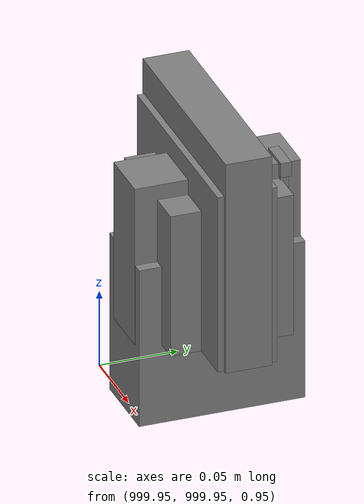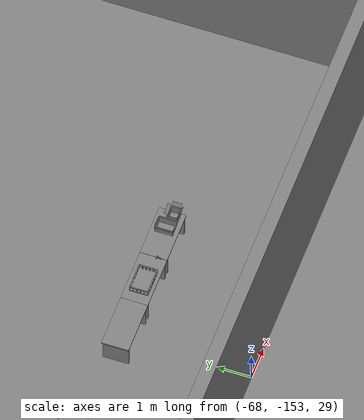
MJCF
<mujoco>
    <option gravity="0.000000000 0.000000000 -9.810000420" timestep="0.0049999999" integrator="implicitfast" density="1.225" viscosity="1.8000001e-05" noslip_iterations="10" iterations="100" sdf_iterations="50">
        <flag multiccd="disable"/>
    </option>
    <size memory="1000M"/>
    <compiler coordinate="local"/>
    <worldbody>
        <light cutoff="30" pos="0 1 1" dir="0 -1 -2"/>
        <light cutoff="30" pos="0 -1 1" dir="0 1 -2"/>
        <body pos="-64.866622925 -149.383972168 30.183746338" euler="89.999984741 89.999946594 0.000000000" name="openloong_gripper_2f85_fix_base_usda_bluebox_01">
            <geom contype="1" conaffinity="1" density="1000" type="box" material="" rgba="0.500000000 0.500000000 0.500000000 1.000000000" solimp="0.899999976 0.949999988 0.001000000" friction="1.000000000 0.005000000 0.000100000" solref="0.020000000 1.000000000" margin="0" condim="3" group="0" pos="0.276580811 0.187225342 0.000068665" quat="0.707106948 0.000077471 0.707106352 0.000077486" size="0.100000001 0.057999998 0.010000000" name="openloong_gripper_2f85_fix_base_usda_geom_5B508A05_205A_45F0_96BF_9BCDB977A7B3"/>
            <geom contype="1" conaffinity="1" density="1000" type="box" material="" rgba="0.500000000 0.500000000 0.500000000 1.000000000" solimp="0.899999976 0.949999988 0.001000000" friction="1.000000000 0.005000000 0.000100000" solref="0.020000000 1.000000000" margin="0" condim="3" group="0" pos="0.000000000 0.002883911 0.000000000" quat="0.999999881 0.000000000 0.000000000 0.000000000" size="0.254000008 0.003000000 0.172000006" name="openloong_gripper_2f85_fix_base_usda_geom_705615CF_56E0_4D0B_94A6_78153CBDE100"/>
            <geom contype="1" conaffinity="1" density="1000" type="box" material="" rgba="0.500000000 0.500000000 0.500000000 1.000000000" solimp="0.899999976 0.949999988 0.001000000" friction="1.000000000 0.005000000 0.000100000" solref="0.020000000 1.000000000" margin="0" condim="3" group="0" pos="0.000000000 0.124874115 0.173484802" quat="0.999796331 0.020176515 -0.000000015 0.000000030" size="0.259999990 0.119999997 0.007000000" name="openloong_gripper_2f85_fix_base_usda_geom_BD9BD6A6_FD33_472E_94B2_49AF9BB6B1C2"/>
            <geom contype="1" conaffinity="1" density="1000" type="box" material="" rgba="0.500000000 0.500000000 0.500000000 1.000000000" solimp="0.899999976 0.949999988 0.001000000" friction="1.000000000 0.005000000 0.000100000" solref="0.020000000 1.000000000" margin="0" condim="3" group="0" pos="0.000000000 0.124874115 -0.173469543" quat="0.999796331 -0.020176545 -0.000000015 0.000000000" size="0.259999990 0.119999997 0.007000000" name="openloong_gripper_2f85_fix_base_usda_geom_6A453975_E717_458F_AFB5_0DB08EAAEA3F"/>
            <geom contype="1" conaffinity="1" density="1000" type="box" material="" rgba="0.500000000 0.500000000 0.500000000 1.000000000" solimp="0.899999976 0.949999988 0.001000000" friction="1.000000000 0.005000000 0.000100000" solref="0.020000000 1.000000000" margin="0" condim="3" group="0" pos="0.000000000 0.214008331 0.188980103" quat="0.999912977 0.013176724 0.000000015 0.000000000" size="0.259999990 0.029999999 0.012500000" name="openloong_gripper_2f85_fix_base_usda_geom_5A04C5E1_11C1_41B9_BAD0_CA7C798ACEA2"/>
            <geom contype="1" conaffinity="1" density="1000" type="box" material="" rgba="0.500000000 0.500000000 0.500000000 1.000000000" solimp="0.899999976 0.949999988 0.001000000" friction="1.000000000 0.005000000 0.000100000" solref="0.020000000 1.000000000" margin="0" condim="3" group="0" pos="-0.258361816 0.125289917 0.001876831" quat="0.702796936 -0.020792112 0.710783124 0.020769298" size="0.189999998 0.119999997 0.009000000" name="openloong_gripper_2f85_fix_base_usda_geom_84C584D4_1FCC_465B_B4B9_3E0D231A619C"/>
            <geom contype="1" conaffinity="1" density="1000" type="box" material="" rgba="0.500000000 0.500000000 0.500000000 1.000000000" solimp="0.899999976 0.949999988 0.001000000" friction="1.000000000 0.005000000 0.000100000" solref="0.020000000 1.000000000" margin="0" condim="3" group="0" pos="0.000000000 0.214008331 -0.188980103" quat="0.999912977 -0.013176769 0.000000030 0.000000015" size="0.259999990 0.029999999 0.012500000" name="openloong_gripper_2f85_fix_base_usda_geom_562D736B_CB0B_48C5_95C4_F84C2A6D25BE"/>
            <geom contype="1" conaffinity="1" density="1000" type="box" material="" rgba="0.500000000 0.500000000 0.500000000 1.000000000" solimp="0.899999976 0.949999988 0.001000000" friction="1.000000000 0.005000000 0.000100000" solref="0.020000000 1.000000000" margin="0" condim="3" group="0" pos="-0.276611328 0.187225342 0.000068665" quat="0.707106650 0.000077441 0.707106709 0.000077456" size="0.100000001 0.057999998 0.010000000" name="openloong_gripper_2f85_fix_base_usda_geom_76A6774B_DB3C_4A53_AC85_EDD510A7669D"/>
            <geom contype="1" conaffinity="1" density="1000" type="box" material="" rgba="0.500000000 0.500000000 0.500000000 1.000000000" solimp="0.899999976 0.949999988 0.001000000" friction="1.000000000 0.005000000 0.000100000" solref="0.020000000 1.000000000" margin="0" condim="3" group="0" pos="0.258331299 0.125289917 0.001876831" quat="0.702851415 0.018856421 0.710823774 -0.019329369" size="0.189999998 0.119999997 0.009000000" name="openloong_gripper_2f85_fix_base_usda_geom_9E14F0EC_0739_45C4_B589_690FAD47FE75"/>
            <freejoint name="openloong_gripper_2f85_fix_base_usda_bluebox_01_joint"/>
            <site size="0.005000000 0.005000000 0.005000000" rgba="0.500000000 0.500000000 0.500000000 1.000000000" pos="0.000000000 0.000000000 0.000000000" quat="0.999961913 0.008726534 0.000000000 0.000000000" group="0" type="sphere" name="openloong_gripper_2f85_fix_base_usda_bluebox_01site"/>
        </body>
        <body pos="-64.496299744 -149.491867065 30.235729218" euler="0.000000000 0.000000000 89.999946594" name="openloong_gripper_2f85_fix_base_usda_cardboardbox_01">
            <geom contype="1" conaffinity="1" density="1000" type="box" material="" rgba="0.500000000 0.500000000 0.500000000 1.000000000" solimp="0.899999976 0.949999988 0.001000000" friction="1.000000000 0.005000000 0.000100000" solref="0.020000000 1.000000000" margin="0" condim="3" group="0" pos="-0.003166199 -0.004086494 0.005052090" quat="1.000000000 0.000000000 0.000000000 0.000000000" size="0.142499998 0.177500010 0.005000000" name="openloong_gripper_2f85_fix_base_usda_geom_2512E673_EC53_4A1C_9E46_CBF43E80C312"/>
            <geom contype="1" conaffinity="1" density="1000" type="box" material="" rgba="0.500000000 0.500000000 0.500000000 1.000000000" solimp="0.899999976 0.949999988 0.001000000" friction="1.000000000 0.005000000 0.000100000" solref="0.020000000 1.000000000" margin="0" condim="3" group="0" pos="-0.003166199 0.170316696 0.150570869" quat="1.000000000 0.000000000 0.000000000 0.000000000" size="0.142499998 0.005000000 0.149999991" name="openloong_gripper_2f85_fix_base_usda_geom_57648FCD_96DC_4AE8_9D73_AB87B4B9EB66"/>
            <geom contype="1" conaffinity="1" density="1000" type="box" material="" rgba="0.500000000 0.500000000 0.500000000 1.000000000" solimp="0.899999976 0.949999988 0.001000000" friction="1.000000000 0.005000000 0.000100000" solref="0.020000000 1.000000000" margin="0" condim="3" group="0" pos="-0.147399902 -0.005307198 0.150570869" quat="1.000000000 0.000000000 0.000000000 0.000000000" size="0.005000000 0.177500010 0.149999991" name="openloong_gripper_2f85_fix_base_usda_geom_99A307E1_243F_4937_BF09_8D8A7EE00DB1"/>
            <geom contype="1" conaffinity="1" density="1000" type="box" material="" rgba="0.500000000 0.500000000 0.500000000 1.000000000" solimp="0.899999976 0.949999988 0.001000000" friction="1.000000000 0.005000000 0.000100000" solref="0.020000000 1.000000000" margin="0" condim="3" group="0" pos="0.140275955 -0.005307198 0.150570869" quat="1.000000000 0.000000000 0.000000000 0.000000000" size="0.005000000 0.177500010 0.149999991" name="openloong_gripper_2f85_fix_base_usda_geom_73BC4BFB_5539_49B8_83E1_E157D86189CF"/>
            <geom contype="1" conaffinity="1" density="1000" type="box" material="" rgba="0.500000000 0.500000000 0.500000000 1.000000000" solimp="0.899999976 0.949999988 0.001000000" friction="1.000000000 0.005000000 0.000100000" solref="0.020000000 1.000000000" margin="0" condim="3" group="0" pos="-0.003166199 -0.181550980 0.150570869" quat="1.000000000 0.000000000 0.000000000 0.000000000" size="0.142499998 0.005000000 0.149999991" name="openloong_gripper_2f85_fix_base_usda_geom_661DAD0C_B497_49F0_B648_BE64E94F2857"/>
            <freejoint name="openloong_gripper_2f85_fix_base_usda_cardboardbox_01_joint"/>
            <site size="0.005000000 0.005000000 0.005000000" rgba="0.500000000 0.500000000 0.500000000 1.000000000" pos="0.000000000 0.000000000 0.000000000" quat="0.999961913 0.008726535 0.000000000 0.000000000" group="0" type="sphere" name="openloong_gripper_2f85_fix_base_usda_site_AEBFC74C_8E3F_4BBA_B134_4D2CB00D2F67"/>
            <body pos="0.139160156 -0.004048347 0.301930904" euler="-179.999954224 49.383502960 179.999954224" name="openloong_gripper_2f85_fix_base_usda_A1_006">
                <geom contype="1" conaffinity="1" density="1000" type="box" material="" rgba="0.500000000 0.500000000 0.500000000 1.000000000" solimp="0.899999976 0.949999988 0.001000000" friction="1.000000000 0.005000000 0.000100000" solref="0.020000000 1.000000000" margin="0" condim="3" group="0" pos="-0.071587563 0.000009537 0.001745224" quat="0.999999881 0.000000000 0.000000000 0.000000000" size="0.071249999 0.179999992 0.002500000" name="openloong_gripper_2f85_fix_base_usda_geom_3664BEEB_B091_49EB_A3D5_525F3EFC3997"/>
                <joint armature="0" stiffness="0.07" damping="0.0099999998" axis="0.000000 1.000000 0.000000" type="hinge" name="openloong_gripper_2f85_fix_base_usda_A1_006"/>
            </body>
            <body pos="-0.145902634 -0.004086494 0.301938057" euler="-180.000000000 -60.000011444 -180.000000000" name="openloong_gripper_2f85_fix_base_usda_A2_006">
                <geom contype="1" conaffinity="1" density="1000" type="box" material="" rgba="0.500000000 0.500000000 0.500000000 1.000000000" solimp="0.899999976 0.949999988 0.001000000" friction="1.000000000 0.005000000 0.000100000" solref="0.020000000 1.000000000" margin="0" condim="3" group="0" pos="0.071268082 0.000009537 0.002717972" quat="0.000002921 0.000000000 -0.000000030 0.999999881" size="0.071249999 0.179999992 0.002500000" name="openloong_gripper_2f85_fix_base_usda_geom_D3A5A339_E867_46F4_9473_22A09A132249"/>
                <joint armature="0" stiffness="0.07" damping="0.0099999998" axis="0.000000 1.000000 0.000000" type="hinge" name="openloong_gripper_2f85_fix_base_usda_A2_006"/>
            </body>
            <body pos="-0.003385544 0.175991058 0.301930904" euler="-125.858116150 -0.000004561 0.000002331" name="openloong_gripper_2f85_fix_base_usda_B2_006">
                <geom contype="1" conaffinity="1" density="1000" type="box" material="" rgba="0.500000000 0.500000000 0.500000000 1.000000000" solimp="0.899999976 0.949999988 0.001000000" friction="1.000000000 0.005000000 0.000100000" solref="0.020000000 1.000000000" margin="0" condim="3" group="0" pos="0.000009537 -0.070939064 -0.002470016" quat="0.999614120 0.027776197 -0.000000015 0.000000030" size="0.137500003 0.064999998 0.005000000" name="openloong_gripper_2f85_fix_base_usda_geom_F445DB0C_0BFB_4A48_8F35_EFA207D9CF01"/>
                <joint armature="0" stiffness="0.07" damping="0.0099999998" axis="1.000000 0.000000 0.000000" type="hinge" name="openloong_gripper_2f85_fix_base_usda_B2_006"/>
            </body>
            <body pos="-0.003385544 -0.184140205 0.301938057" euler="147.805557251 0.000000000 0.000000000" name="openloong_gripper_2f85_fix_base_usda_B1_006">
                <geom contype="1" conaffinity="1" density="1000" type="box" material="" rgba="0.500000000 0.500000000 0.500000000 1.000000000" solimp="0.899999976 0.949999988 0.001000000" friction="1.000000000 0.005000000 0.000100000" solref="0.020000000 1.000000000" margin="0" condim="3" group="0" pos="-0.000028610 0.070202351 -0.002703667" quat="0.999614179 -0.027776167 0.000000000 0.000000000" size="0.137500003 0.064999998 0.005000000" name="openloong_gripper_2f85_fix_base_usda_geom_346089E5_074F_4B69_A755_77CDDEB5469C"/>
                <joint armature="0" stiffness="0.07" damping="0.0099999998" axis="1.000000 0.000000 0.000000" type="hinge" name="openloong_gripper_2f85_fix_base_usda_B1_006"/>
            </body>
        </body>
        <body pos="-65.882858276 -149.481979370 30.229999542" euler="-64.487716675 0.000000000 0.000000000" name="openloong_gripper_2f85_fix_base_usda_Barcode">
            <geom contype="1" conaffinity="1" density="1000" type="box" material="" rgba="0.500000000 0.500000000 0.500000000 1.000000000" solimp="0.899999976 0.949999988 0.001000000" friction="1.000000000 0.005000000 0.000100000" solref="0.020000000 1.000000000" margin="0" condim="3" group="0" pos="0.000000000 0.013038635 0.001419067" quat="0.000000000 0.000000000 0.000000000 1.000000119" size="0.034000002 0.010000000 0.017999999" name="openloong_gripper_2f85_fix_base_usda_geom_4AD4BD20_E555_42F5_B99D_D38CC42B19B1"/>
            <geom contype="1" conaffinity="1" density="1000" type="box" material="" rgba="0.500000000 0.500000000 0.500000000 1.000000000" solimp="0.899999976 0.949999988 0.001000000" friction="1.000000000 0.005000000 0.000100000" solref="0.020000000 1.000000000" margin="0" condim="3" group="0" pos="0.000000000 -0.035301208 -0.007095337" quat="0.000000000 0.000000000 -0.043619365 0.999048233" size="0.028999999 0.010000000 0.020000000" name="openloong_gripper_2f85_fix_base_usda_geom_E0D25662_7ACA_4A79_9FEB_7DFE27BBE234"/>
            <geom contype="1" conaffinity="1" density="1000" type="box" material="" rgba="0.500000000 0.500000000 0.500000000 1.000000000" solimp="0.899999976 0.949999988 0.001000000" friction="1.000000000 0.005000000 0.000100000" solref="0.020000000 1.000000000" margin="0" condim="3" group="0" pos="0.000000000 -0.043411255 -0.011749268" quat="0.922262907 0.386563420 0.000000000 0.000000000" size="0.026000001 0.010000000 0.020000000" name="openloong_gripper_2f85_fix_base_usda_geom_04672547_82ED_4A1A_9169_2D22E7F34E37"/>
            <geom contype="1" conaffinity="1" density="1000" type="box" material="" rgba="0.500000000 0.500000000 0.500000000 1.000000000" solimp="0.899999976 0.949999988 0.001000000" friction="1.000000000 0.005000000 0.000100000" solref="0.020000000 1.000000000" margin="0" condim="3" group="0" pos="0.000000000 -0.016967773 -0.031860352" quat="0.000000000 0.000000000 0.000000000 1.000000119" size="0.008000000 0.010000000 0.013000000" name="openloong_gripper_2f85_fix_base_usda_geom_310FEFAE_AEB9_4240_8653_5BDEA35205D0"/>
            <geom contype="1" conaffinity="1" density="1000" type="box" material="" rgba="0.500000000 0.500000000 0.500000000 1.000000000" solimp="0.899999976 0.949999988 0.001000000" friction="1.000000000 0.005000000 0.000100000" solref="0.020000000 1.000000000" margin="0" condim="3" group="0" pos="0.000000000 -0.001869202 0.000312805" quat="0.953716993 0.300705761 0.000000000 0.000000000" size="0.032000002 0.010000000 0.018999999" name="openloong_gripper_2f85_fix_base_usda_geom_A7609686_D7BD_43DE_917A_488C4AF50AC9"/>
            <geom contype="1" conaffinity="1" density="1000" type="box" material="" rgba="0.500000000 0.500000000 0.500000000 1.000000000" solimp="0.899999976 0.949999988 0.001000000" friction="1.000000000 0.005000000 0.000100000" solref="0.020000000 1.000000000" margin="0" condim="3" group="0" pos="0.000000000 -0.019531250 -0.003173828" quat="0.953716993 0.300705761 0.000000000 0.000000000" size="0.030999999 0.010000000 0.020000000" name="openloong_gripper_2f85_fix_base_usda_geom_BA5D3162_3DCA_4A3A_9F9B_BA68FA76B273"/>
            <geom contype="1" conaffinity="1" density="1000" type="box" material="" rgba="0.500000000 0.500000000 0.500000000 1.000000000" solimp="0.899999976 0.949999988 0.001000000" friction="1.000000000 0.005000000 0.000100000" solref="0.020000000 1.000000000" margin="0" condim="3" group="0" pos="0.000000000 -0.035301208 -0.007095337" quat="0.953716993 0.300705761 0.000000000 0.000000000" size="0.028999999 0.010000000 0.020000000" name="openloong_gripper_2f85_fix_base_usda_geom_023A96B3_2977_4808_9BDC_40FB8D2B9D5C"/>
            <geom contype="1" conaffinity="1" density="1000" type="box" material="" rgba="0.500000000 0.500000000 0.500000000 1.000000000" solimp="0.899999976 0.949999988 0.001000000" friction="1.000000000 0.005000000 0.000100000" solref="0.020000000 1.000000000" margin="0" condim="3" group="0" pos="0.000000000 -0.042617798 -0.071121216" quat="0.000000000 0.000000000 0.000000000 1.000000119" size="0.013000000 0.021000000 0.059999999" name="openloong_gripper_2f85_fix_base_usda_geom_C43E6118_98BA_40A5_A033_C9116C489763"/>
            <freejoint name="openloong_gripper_2f85_fix_base_usda_Barcode_joint"/>
            <site size="0.005000000 0.005000000 0.005000000" rgba="0.500000000 0.500000000 0.500000000 1.000000000" pos="0.000000000 0.000000000 0.000000000" quat="1.000000000 0.000000000 0.000000000 0.000000000" group="0" type="sphere" name="openloong_gripper_2f85_fix_base_usda_Barcode_site"/>
        </body>
        <body pos="-66.745018005 -149.392349243 30.184000015" euler="0.000000000 0.000000000 89.999946594" name="[22331448651579]_Basket_01">
            <geom contype="1" conaffinity="1" density="1000" type="box" material="" rgba="0.500000000 0.500000000 0.500000000 1.000000000" solimp="0.899999976 0.949999988 0.001000000" friction="1.000000000 0.005000000 0.000100000" solref="0.020000000 1.000000000" margin="0" condim="3" group="0" pos="-0.052425385 0.389207840 0.089787483" quat="0.707107008 0.000000000 0.000000000 0.707106411" size="0.014249999 0.014249999 0.059999999" name="[22331448651579]_geom_BFD4951D_C7BC_4B0C_848B_1F6534A421A5"/>
            <geom contype="1" conaffinity="1" density="1000" type="box" material="" rgba="0.500000000 0.500000000 0.500000000 1.000000000" solimp="0.899999976 0.949999988 0.001000000" friction="1.000000000 0.005000000 0.000100000" solref="0.020000000 1.000000000" margin="0" condim="3" group="0" pos="0.264015198 -0.133043289 0.089787483" quat="0.707107008 0.000000000 0.000000000 0.707106411" size="0.014249999 0.014249999 0.059999999" name="[22331448651579]_geom_8321F72B_9354_4EC1_86CE_AF0B134EC463"/>
            <geom contype="1" conaffinity="1" density="1000" type="box" material="" rgba="0.500000000 0.500000000 0.500000000 1.000000000" solimp="0.899999976 0.949999988 0.001000000" friction="1.000000000 0.005000000 0.000100000" solref="0.020000000 1.000000000" margin="0" condim="3" group="0" pos="-0.264015198 -0.265548706 0.089793205" quat="0.707107008 0.000000000 0.000000000 0.707106411" size="0.014249999 0.014249999 0.059999999" name="[22331448651579]_geom_DCF3DE36_0124_4CBA_8B0B_BF9B0759850B"/>
            <geom contype="1" conaffinity="1" density="1000" type="box" material="" rgba="0.500000000 0.500000000 0.500000000 1.000000000" solimp="0.899999976 0.949999988 0.001000000" friction="1.000000000 0.005000000 0.000100000" solref="0.020000000 1.000000000" margin="0" condim="3" group="0" pos="-0.160263062 -0.389322281 0.089793205" quat="0.707107008 0.000000000 0.000000000 0.707106411" size="0.014249999 0.014249999 0.059999999" name="[22331448651579]_geom_ACDC492D_3917_43E6_8D09_D25DA355049A"/>
            <geom contype="1" conaffinity="1" density="1000" type="box" material="" rgba="0.500000000 0.500000000 0.500000000 1.000000000" solimp="0.899999976 0.949999988 0.001000000" friction="1.000000000 0.005000000 0.000100000" solref="0.020000000 1.000000000" margin="0" condim="3" group="0" pos="0.162265778 -0.389322281 0.089787483" quat="0.707107008 0.000000000 0.000000000 0.707106411" size="0.014249999 0.014249999 0.059999999" name="[22331448651579]_geom_BFF6EFAC_DDB2_4F89_8FD8_54063F85C016"/>
            <geom contype="1" conaffinity="1" density="1000" type="box" material="" rgba="0.500000000 0.500000000 0.500000000 1.000000000" solimp="0.899999976 0.949999988 0.001000000" friction="1.000000000 0.005000000 0.000100000" solref="0.020000000 1.000000000" margin="0" condim="3" group="0" pos="0.264015198 0.389207840 0.089787483" quat="0.707107008 0.000000000 0.000000000 0.707106411" size="0.014249999 0.014249999 0.059999999" name="[22331448651579]_geom_A79F9AC4_74FD_4654_B691_9A3DCB1C499A"/>
            <geom contype="1" conaffinity="1" density="1000" type="box" material="" rgba="0.500000000 0.500000000 0.500000000 1.000000000" solimp="0.899999976 0.949999988 0.001000000" friction="1.000000000 0.005000000 0.000100000" solref="0.020000000 1.000000000" margin="0" condim="3" group="0" pos="-0.264015198 -0.133043289 0.089793205" quat="0.707107008 0.000000000 0.000000000 0.707106411" size="0.014249999 0.014249999 0.059999999" name="[22331448651579]_geom_779688AF_41DB_49A5_BA6B_C3BEB65FFE68"/>
            <geom contype="1" conaffinity="1" density="1000" type="box" material="" rgba="0.500000000 0.500000000 0.500000000 1.000000000" solimp="0.899999976 0.949999988 0.001000000" friction="1.000000000 0.005000000 0.000100000" solref="0.020000000 1.000000000" margin="0" condim="3" group="0" pos="-0.264026642 0.269256592 0.089793205" quat="0.707107008 0.000000000 0.000000000 0.707106411" size="0.014249999 0.014249999 0.059999999" name="[22331448651579]_geom_2157B92F_D3CD_447B_8699_644C8D52E0A6"/>
            <geom contype="1" conaffinity="1" density="1000" type="box" material="" rgba="0.500000000 0.500000000 0.500000000 1.000000000" solimp="0.899999976 0.949999988 0.001000000" friction="1.000000000 0.005000000 0.000100000" solref="0.020000000 1.000000000" margin="0" condim="3" group="0" pos="0.054462433 0.389207840 0.089787483" quat="0.707107008 0.000000000 0.000000000 0.707106411" size="0.014249999 0.014249999 0.059999999" name="[22331448651579]_geom_51B78D0D_D87E_42BD_B3DA_95AEEF229A24"/>
            <geom contype="1" conaffinity="1" density="1000" type="box" material="" rgba="0.500000000 0.500000000 0.500000000 1.000000000" solimp="0.899999976 0.949999988 0.001000000" friction="1.000000000 0.005000000 0.000100000" solref="0.020000000 1.000000000" margin="0" condim="3" group="0" pos="0.054462433 -0.389322281 0.089787483" quat="0.707107008 0.000000000 0.000000000 0.707106411" size="0.014249999 0.014249999 0.059999999" name="[22331448651579]_geom_F57A8E12_4805_41D2_85EB_1938D08506BE"/>
            <geom contype="1" conaffinity="1" density="1000" type="box" material="" rgba="0.500000000 0.500000000 0.500000000 1.000000000" solimp="0.899999976 0.949999988 0.001000000" friction="1.000000000 0.005000000 0.000100000" solref="0.020000000 1.000000000" margin="0" condim="3" group="0" pos="0.264015198 0.269256592 0.089793205" quat="0.707107008 0.000000000 0.000000000 0.707106411" size="0.014249999 0.014249999 0.059999999" name="[22331448651579]_geom_C87A4C4E_252A_4523_8E7F_EF97FA420D7E"/>
            <geom contype="1" conaffinity="1" density="1000" type="box" material="" rgba="0.500000000 0.500000000 0.500000000 1.000000000" solimp="0.899999976 0.949999988 0.001000000" friction="1.000000000 0.005000000 0.000100000" solref="0.020000000 1.000000000" margin="0" condim="3" group="0" pos="0.264015198 -0.389322281 0.089787483" quat="0.707107008 0.000000000 0.000000000 0.707106411" size="0.014249999 0.014249999 0.059999999" name="[22331448651579]_geom_A93D57A8_5ADF_4275_9F52_E2C8B5A1A1DB"/>
            <geom contype="1" conaffinity="1" density="1000" type="box" material="" rgba="0.500000000 0.500000000 0.500000000 1.000000000" solimp="0.899999976 0.949999988 0.001000000" friction="1.000000000 0.005000000 0.000100000" solref="0.020000000 1.000000000" margin="0" condim="3" group="0" pos="0.000000000 0.000000000 0.015998840" quat="0.707107008 0.000000000 0.000000000 0.707106411" size="0.403499991 0.279000014 0.015750000" name="[22331448651579]_geom_FA1562EB_D253_4727_8F8A_D4841D8E9A0B"/>
            <geom contype="1" conaffinity="1" density="1000" type="box" material="" rgba="0.500000000 0.500000000 0.500000000 1.000000000" solimp="0.899999976 0.949999988 0.001000000" friction="1.000000000 0.005000000 0.000100000" solref="0.020000000 1.000000000" margin="0" condim="3" group="0" pos="0.000000000 -0.389476776 0.163619041" quat="0.707107008 0.000000000 0.000000000 0.707106411" size="0.015000000 0.277500004 0.015750000" name="[22331448651579]_geom_8D79A217_397D_44BF_AFBC_B3385C583B01"/>
            <geom contype="1" conaffinity="1" density="1000" type="box" material="" rgba="0.500000000 0.500000000 0.500000000 1.000000000" solimp="0.899999976 0.949999988 0.001000000" friction="1.000000000 0.005000000 0.000100000" solref="0.020000000 1.000000000" margin="0" condim="3" group="0" pos="0.162265778 0.389207840 0.089787483" quat="0.707107008 0.000000000 0.000000000 0.707106411" size="0.014249999 0.014249999 0.059999999" name="[22331448651579]_geom_7E267EDA_4CB3_42AF_B6AD_87FC36EC9415"/>
            <geom contype="1" conaffinity="1" density="1000" type="box" material="" rgba="0.500000000 0.500000000 0.500000000 1.000000000" solimp="0.899999976 0.949999988 0.001000000" friction="1.000000000 0.005000000 0.000100000" solref="0.020000000 1.000000000" margin="0" condim="3" group="0" pos="0.000000000 0.389471054 0.163619041" quat="0.707107008 0.000000000 0.000000000 0.707106411" size="0.015000000 0.277500004 0.015750000" name="[22331448651579]_geom_893C7B1D_12F9_4DE2_9B3D_4115F6C36EB4"/>
            <geom contype="1" conaffinity="1" density="1000" type="box" material="" rgba="0.500000000 0.500000000 0.500000000 1.000000000" solimp="0.899999976 0.949999988 0.001000000" friction="1.000000000 0.005000000 0.000100000" solref="0.020000000 1.000000000" margin="0" condim="3" group="0" pos="-0.263511658 0.000000000 0.163619041" quat="0.707107008 0.000000000 0.000000000 0.707106411" size="0.403499991 0.015000000 0.015750000" name="[22331448651579]_geom_540AD7CA_DAE6_473D_B66A_C58B9627C729"/>
            <geom contype="1" conaffinity="1" density="1000" type="box" material="" rgba="0.500000000 0.500000000 0.500000000 1.000000000" solimp="0.899999976 0.949999988 0.001000000" friction="1.000000000 0.005000000 0.000100000" solref="0.020000000 1.000000000" margin="0" condim="3" group="0" pos="-0.264015198 0.141334534 0.089793205" quat="0.707107008 0.000000000 0.000000000 0.707106411" size="0.014249999 0.014249999 0.059999999" name="[22331448651579]_geom_E925BB4A_08C7_4208_B850_4433E966F750"/>
            <geom contype="1" conaffinity="1" density="1000" type="box" material="" rgba="0.500000000 0.500000000 0.500000000 1.000000000" solimp="0.899999976 0.949999988 0.001000000" friction="1.000000000 0.005000000 0.000100000" solref="0.020000000 1.000000000" margin="0" condim="3" group="0" pos="0.264015198 -0.265548706 0.089787483" quat="0.707107008 0.000000000 0.000000000 0.707106411" size="0.014249999 0.014249999 0.059999999" name="[22331448651579]_geom_4445AB51_2D3F_4378_B414_0E9508047616"/>
            <geom contype="1" conaffinity="1" density="1000" type="box" material="" rgba="0.500000000 0.500000000 0.500000000 1.000000000" solimp="0.899999976 0.949999988 0.001000000" friction="1.000000000 0.005000000 0.000100000" solref="0.020000000 1.000000000" margin="0" condim="3" group="0" pos="-0.160263062 0.389207840 0.089787483" quat="0.707107008 0.000000000 0.000000000 0.707106411" size="0.014249999 0.014249999 0.059999999" name="[22331448651579]_geom_84A3A645_2E20_48FB_8FCB_0A0488C18F97"/>
            <geom contype="1" conaffinity="1" density="1000" type="box" material="" rgba="0.500000000 0.500000000 0.500000000 1.000000000" solimp="0.899999976 0.949999988 0.001000000" friction="1.000000000 0.005000000 0.000100000" solref="0.020000000 1.000000000" margin="0" condim="3" group="0" pos="-0.052425385 -0.389322281 0.089787483" quat="0.707107008 0.000000000 0.000000000 0.707106411" size="0.014249999 0.014249999 0.059999999" name="[22331448651579]_geom_6FF81D86_EE92_4AB1_B28C_BE55E68EC291"/>
            <geom contype="1" conaffinity="1" density="1000" type="box" material="" rgba="0.500000000 0.500000000 0.500000000 1.000000000" solimp="0.899999976 0.949999988 0.001000000" friction="1.000000000 0.005000000 0.000100000" solref="0.020000000 1.000000000" margin="0" condim="3" group="0" pos="-0.264026642 -0.389322281 0.089793205" quat="0.707107008 0.000000000 0.000000000 0.707106411" size="0.014249999 0.014249999 0.059999999" name="[22331448651579]_geom_71C576C4_2BE4_48DE_9507_404BCF5699EA"/>
            <geom contype="1" conaffinity="1" density="1000" type="box" material="" rgba="0.500000000 0.500000000 0.500000000 1.000000000" solimp="0.899999976 0.949999988 0.001000000" friction="1.000000000 0.005000000 0.000100000" solref="0.020000000 1.000000000" margin="0" condim="3" group="0" pos="0.264015198 0.141334534 0.089787483" quat="0.707107008 0.000000000 0.000000000 0.707106411" size="0.014249999 0.014249999 0.059999999" name="[22331448651579]_geom_6F8A4C70_F272_4860_A973_AFE9E5753B53"/>
            <geom contype="1" conaffinity="1" density="1000" type="box" material="" rgba="0.500000000 0.500000000 0.500000000 1.000000000" solimp="0.899999976 0.949999988 0.001000000" friction="1.000000000 0.005000000 0.000100000" solref="0.020000000 1.000000000" margin="0" condim="3" group="0" pos="-0.264015198 0.389207840 0.089793205" quat="0.707107008 0.000000000 0.000000000 0.707106411" size="0.014249999 0.014249999 0.059999999" name="[22331448651579]_geom_F6BEA3A7_0424_4C80_9CAF_4EDAC4536863"/>
            <geom contype="1" conaffinity="1" density="1000" type="box" material="" rgba="0.500000000 0.500000000 0.500000000 1.000000000" solimp="0.899999976 0.949999988 0.001000000" friction="1.000000000 0.005000000 0.000100000" solref="0.020000000 1.000000000" margin="0" condim="3" group="0" pos="0.264015198 0.004480362 0.089787483" quat="0.707107008 0.000000000 0.000000000 0.707106411" size="0.014249999 0.014249999 0.059999999" name="[22331448651579]_geom_E0EB8F91_51B8_4611_8F58_33EA8B5BB8F2"/>
            <geom contype="1" conaffinity="1" density="1000" type="box" material="" rgba="0.500000000 0.500000000 0.500000000 1.000000000" solimp="0.899999976 0.949999988 0.001000000" friction="1.000000000 0.005000000 0.000100000" solref="0.020000000 1.000000000" margin="0" condim="3" group="0" pos="0.263694763 -0.000011444 0.163619041" quat="0.707107008 0.000000000 0.000000000 0.707106411" size="0.403499991 0.015000000 0.015750000" name="[22331448651579]_geom_398EA58B_9D17_4B75_8044_2F7EEDE1D0E6"/>
            <geom contype="1" conaffinity="1" density="1000" type="box" material="" rgba="0.500000000 0.500000000 0.500000000 1.000000000" solimp="0.899999976 0.949999988 0.001000000" friction="1.000000000 0.005000000 0.000100000" solref="0.020000000 1.000000000" margin="0" condim="3" group="0" pos="-0.264015198 0.004480362 0.089793205" quat="0.707107008 0.000000000 0.000000000 0.707106411" size="0.014249999 0.014249999 0.059999999" name="[22331448651579]_geom_22AD3539_7FB3_4FD8_95D5_757EECFD3660"/>
            <freejoint name="[22331448651579]_joint_38D76613_0227_49A2_A771_196E3054ACA7"/>
        </body>
        <body pos="0.000000000 0.000000000 0.000000000" euler="0.000000000 0.000000000 0.000000000" name="Static Objects_Static Objects">
            <geom contype="1" conaffinity="1" density="1000" type="box" material="" rgba="0.500000000 0.500000000 0.500000000 1.000000000" solimp="0.899999976 0.949999988 0.001000000" friction="1.000000000 0.005000000 0.000100000" solref="0.020000000 1.000000000" margin="0" condim="3" group="0" pos="-67.544113159 -149.365814209 29.727830887" quat="0.500000417 0.499999970 0.499999553 0.499999970" size="0.381000012 0.319999993 0.041000001" name="Static Objects_geom_33B2E7D1_923B_4174_B3A7_A6CB2CE98F40"/>
            <geom contype="1" conaffinity="1" density="1000" type="box" material="" rgba="0.500000000 0.500000000 0.500000000 1.000000000" solimp="0.899999976 0.949999988 0.001000000" friction="1.000000000 0.005000000 0.000100000" solref="0.020000000 1.000000000" margin="0" condim="3" group="0" pos="-68.239501953 -149.365814209 30.086868286" quat="0.500000417 0.499999970 0.499999553 0.499999970" size="0.370999992 0.039500002 0.745000005" name="Static Objects_geom_3EC64513_634B_4B87_9F76_874D281CC43D"/>
            <geom contype="1" conaffinity="1" density="1000" type="box" material="" rgba="0.500000000 0.500000000 0.500000000 1.000000000" solimp="0.899999976 0.949999988 0.001000000" friction="1.000000000 0.005000000 0.000100000" solref="0.020000000 1.000000000" margin="0" condim="3" group="0" pos="-68.239501953 -149.365814209 30.147235870" quat="0.500000417 0.499999970 0.499999553 0.499999970" size="0.400000006 0.022000000 0.800000012" name="Static Objects_geom_679555BC_1F05_464E_AF98_D254A0A67D4B"/>
            <geom contype="1" conaffinity="1" density="1000" type="box" material="" rgba="0.500000000 0.500000000 0.500000000 1.000000000" solimp="0.899999976 0.949999988 0.001000000" friction="1.000000000 0.005000000 0.000100000" solref="0.020000000 1.000000000" margin="0" condim="3" group="0" pos="-68.934890747 -149.365814209 29.727830887" quat="0.500000417 0.499999970 0.499999553 0.499999970" size="0.381000012 0.319999993 0.041000001" name="Static Objects_geom_B990D436_186D_42B9_B20C_F9A599B9B474"/>
            <geom contype="1" conaffinity="1" density="1000" type="box" material="" rgba="0.500000000 0.500000000 0.500000000 1.000000000" solimp="0.899999976 0.949999988 0.001000000" friction="1.000000000 0.005000000 0.000100000" solref="0.020000000 1.000000000" margin="0" condim="3" group="0" pos="-68.239501953 -149.365814209 29.561563492" quat="0.500000417 0.499999970 0.499999553 0.499999970" size="0.020000000 0.022000000 0.660000026" name="Static Objects_geom_670C690B_0776_43BB_9D33_3B681E9BB68C"/>
            <geom contype="1" conaffinity="1" density="1000" type="box" material="" rgba="0.500000000 0.500000000 0.500000000 1.000000000" solimp="0.899999976 0.949999988 0.001000000" friction="1.000000000 0.005000000 0.000100000" solref="0.020000000 1.000000000" margin="0" condim="3" group="0" pos="-65.945671082 -149.365814209 29.727830887" quat="0.500000417 0.499999970 0.499999553 0.499999970" size="0.381000012 0.319999993 0.041000001" name="Static Objects_geom_D9F95027_EA32_4DEF_B4DA_CF44DA0B0CA6"/>
            <geom contype="1" conaffinity="1" density="1000" type="box" material="" rgba="0.500000000 0.500000000 0.500000000 1.000000000" solimp="0.899999976 0.949999988 0.001000000" friction="1.000000000 0.005000000 0.000100000" solref="0.020000000 1.000000000" margin="0" condim="3" group="0" pos="-66.641059875 -149.365814209 30.086868286" quat="0.500000417 0.499999970 0.499999553 0.499999970" size="0.370999992 0.039500002 0.745000005" name="Static Objects_geom_9E412F56_FFF6_4B94_88DB_F5540CAF27D0"/>
            <geom contype="1" conaffinity="1" density="1000" type="box" material="" rgba="0.500000000 0.500000000 0.500000000 1.000000000" solimp="0.899999976 0.949999988 0.001000000" friction="1.000000000 0.005000000 0.000100000" solref="0.020000000 1.000000000" margin="0" condim="3" group="0" pos="-66.641059875 -149.365814209 30.147235870" quat="0.500000417 0.499999970 0.499999553 0.499999970" size="0.400000006 0.022000000 0.800000012" name="Static Objects_geom_F02E825B_89DD_4404_9312_714A9AD4563B"/>
            <geom contype="1" conaffinity="1" density="1000" type="box" material="" rgba="0.500000000 0.500000000 0.500000000 1.000000000" solimp="0.899999976 0.949999988 0.001000000" friction="1.000000000 0.005000000 0.000100000" solref="0.020000000 1.000000000" margin="0" condim="3" group="0" pos="-67.336448669 -149.365814209 29.727830887" quat="0.500000417 0.499999970 0.499999553 0.499999970" size="0.381000012 0.319999993 0.041000001" name="Static Objects_geom_189079CA_977C_4E40_8BC1_1FCC3040B46A"/>
            <geom contype="1" conaffinity="1" density="1000" type="box" material="" rgba="0.500000000 0.500000000 0.500000000 1.000000000" solimp="0.899999976 0.949999988 0.001000000" friction="1.000000000 0.005000000 0.000100000" solref="0.020000000 1.000000000" margin="0" condim="3" group="0" pos="-66.641059875 -149.365814209 29.561563492" quat="0.500000417 0.499999970 0.499999553 0.499999970" size="0.020000000 0.022000000 0.660000026" name="Static Objects_geom_88ADBF0B_6F52_466B_8B48_BFF14B2CDE54"/>
            <geom contype="1" conaffinity="1" density="1000" type="box" material="" rgba="0.500000000 0.500000000 0.500000000 1.000000000" solimp="0.899999976 0.949999988 0.001000000" friction="1.000000000 0.005000000 0.000100000" solref="0.020000000 1.000000000" margin="0" condim="3" group="0" pos="-64.338577271 -149.365814209 29.727830887" quat="0.500000417 0.499999970 0.499999553 0.499999970" size="0.381000012 0.319999993 0.041000001" name="Static Objects_geom_4CC61BFB_2299_4BF2_9DB9_A049F0F027DD"/>
            <geom contype="1" conaffinity="1" density="1000" type="box" material="" rgba="0.500000000 0.500000000 0.500000000 1.000000000" solimp="0.899999976 0.949999988 0.001000000" friction="1.000000000 0.005000000 0.000100000" solref="0.020000000 1.000000000" margin="0" condim="3" group="0" pos="-65.033966064 -149.365814209 30.086868286" quat="0.500000417 0.499999970 0.499999553 0.499999970" size="0.370999992 0.039500002 0.745000005" name="Static Objects_geom_6EAD19A4_B568_43FB_BB1C_A2351BF4D060"/>
            <geom contype="1" conaffinity="1" density="1000" type="box" material="" rgba="0.500000000 0.500000000 0.500000000 1.000000000" solimp="0.899999976 0.949999988 0.001000000" friction="1.000000000 0.005000000 0.000100000" solref="0.020000000 1.000000000" margin="0" condim="3" group="0" pos="-65.033966064 -149.365814209 30.147235870" quat="0.500000417 0.499999970 0.499999553 0.499999970" size="0.400000006 0.022000000 0.800000012" name="Static Objects_geom_9F7AF138_6B7D_48FE_AC17_BDF8B99C6C97"/>
            <geom contype="1" conaffinity="1" density="1000" type="box" material="" rgba="0.500000000 0.500000000 0.500000000 1.000000000" solimp="0.899999976 0.949999988 0.001000000" friction="1.000000000 0.005000000 0.000100000" solref="0.020000000 1.000000000" margin="0" condim="3" group="0" pos="-65.729354858 -149.365814209 29.727830887" quat="0.500000417 0.499999970 0.499999553 0.499999970" size="0.381000012 0.319999993 0.041000001" name="Static Objects_geom_C1DFEF63_2B92_4ABA_813A_CC6E97398467"/>
            <geom contype="1" conaffinity="1" density="1000" type="box" material="" rgba="0.500000000 0.500000000 0.500000000 1.000000000" solimp="0.899999976 0.949999988 0.001000000" friction="1.000000000 0.005000000 0.000100000" solref="0.020000000 1.000000000" margin="0" condim="3" group="0" pos="-65.033966064 -149.365814209 29.561563492" quat="0.500000417 0.499999970 0.499999553 0.499999970" size="0.020000000 0.022000000 0.660000026" name="Static Objects_geom_8BA3644D_725A_4834_8168_300F947C0D86"/>
            <geom contype="1" conaffinity="1" density="1000" type="box" material="" rgba="0.500000000 0.500000000 0.500000000 1.000000000" solimp="0.899999976 0.949999988 0.001000000" friction="1.000000000 0.005000000 0.000100000" solref="0.020000000 1.000000000" margin="0" condim="3" group="0" pos="-61.754566193 -137.853729248 33.906845093" quat="0.707107067 0.000000000 0.000000000 0.707106471" size="0.759999990 0.759999990 4.500000000" name="Static Objects_geom_BEACB8F6_9AF7_4879_B46B_D3AB0B2F8B1E"/>
            <geom contype="1" conaffinity="1" density="1000" type="box" material="" rgba="0.500000000 0.500000000 0.500000000 1.000000000" solimp="0.899999976 0.949999988 0.001000000" friction="1.000000000 0.005000000 0.000100000" solref="0.020000000 1.000000000" margin="0" condim="3" group="0" pos="-57.511135101 -144.927108765 31.707921982" quat="1.000000000 0.000000000 0.000000000 0.000000000" size="0.200000003 8.000000000 2.299999952" name="Static Objects_geom_06B605D1_08C1_4822_BEA7_35273DCD778D"/>
            <geom contype="1" conaffinity="1" density="1000" type="box" material="" rgba="0.500000000 0.500000000 0.500000000 1.000000000" solimp="0.899999976 0.949999988 0.001000000" friction="1.000000000 0.005000000 0.000100000" solref="0.020000000 1.000000000" margin="0" condim="3" group="0" pos="-80.517646790 -157.574050903 31.688196182" quat="0.707107067 0.000000000 0.000000000 0.707106471" size="0.600000024 0.600000024 2.299999952" name="Static Objects_geom_270FFBCC_6791_49F2_9239_6D1D124D3A72"/>
            <geom contype="1" conaffinity="1" density="1000" type="box" material="" rgba="0.500000000 0.500000000 0.500000000 1.000000000" solimp="0.899999976 0.949999988 0.001000000" friction="1.000000000 0.005000000 0.000100000" solref="0.020000000 1.000000000" margin="0" condim="3" group="0" pos="-80.711044312 -147.414932251 31.666158676" quat="1.000000000 0.000000000 0.000000000 0.000000000" size="0.200000003 10.000000000 2.299999952" name="Static Objects_geom_D0BA32FF_14D5_4B6B_8378_633BAB69D1DD"/>
            <geom contype="1" conaffinity="1" density="1000" type="box" material="" rgba="0.500000000 0.500000000 0.500000000 1.000000000" solimp="0.899999976 0.949999988 0.001000000" friction="1.000000000 0.005000000 0.000100000" solref="0.020000000 1.000000000" margin="0" condim="3" group="0" pos="-57.687217712 -137.434692383 31.688196182" quat="0.707107067 0.000000000 0.000000000 0.707106471" size="0.600000024 0.600000024 2.299999952" name="Static Objects_geom_87D960C5_C80A_452C_98F6_CBBB3CF38304"/>
            <geom contype="1" conaffinity="1" density="1000" type="box" material="" rgba="0.500000000 0.500000000 0.500000000 1.000000000" solimp="0.899999976 0.949999988 0.001000000" friction="1.000000000 0.005000000 0.000100000" solref="0.020000000 1.000000000" margin="0" condim="3" group="0" pos="-69.537033081 -140.263229370 31.714921951" quat="0.707107067 0.000000000 0.000000000 0.707106471" size="0.759999990 4.500000000 2.299999952" name="Static Objects_geom_DD0A2470_2DD0_4929_991D_5374DB251759"/>
            <geom contype="1" conaffinity="1" density="1000" type="box" material="" rgba="0.500000000 0.500000000 0.500000000 1.000000000" solimp="0.899999976 0.949999988 0.001000000" friction="1.000000000 0.005000000 0.000100000" solref="0.020000000 1.000000000" margin="0" condim="3" group="0" pos="-80.073638916 -137.853713989 33.906845093" quat="0.707107067 0.000000000 0.000000000 0.707106471" size="0.759999990 0.759999990 4.500000000" name="Static Objects_geom_096E34D0_E4F0_42A8_AE12_F7628BF2AEB3"/>
            <geom contype="1" conaffinity="1" density="1000" type="box" material="" rgba="0.500000000 0.500000000 0.500000000 1.000000000" solimp="0.899999976 0.949999988 0.001000000" friction="1.000000000 0.005000000 0.000100000" solref="0.020000000 1.000000000" margin="0" condim="3" group="0" pos="-73.406707764 -155.734664917 31.707921982" quat="1.000000000 0.000000000 0.000000000 0.000000000" size="0.200000003 3.000000000 2.299999952" name="Static Objects_geom_4B4B803B_3060_4415_8C19_66741B7BDC9F"/>
            <geom contype="1" conaffinity="1" density="1000" type="box" material="" rgba="0.500000000 0.500000000 0.500000000 1.000000000" solimp="0.899999976 0.949999988 0.001000000" friction="1.000000000 0.005000000 0.000100000" solref="0.020000000 1.000000000" margin="0" condim="3" group="0" pos="-68.497543335 -137.448257446 31.707921982" quat="0.707107067 0.000000000 0.000000000 0.707106471" size="0.200000003 14.000000000 2.299999952" name="Static Objects_geom_166DEDA2_270B_451B_A00E_808C9B84486A"/>
            <geom contype="1" conaffinity="1" density="1000" type="cylinder" material="" rgba="0.500000000 0.500000000 0.500000000 1.000000000" solimp="0.899999976 0.949999988 0.001000000" friction="1.000000000 0.005000000 0.000100000" solref="0.020000000 1.000000000" margin="0" condim="3" group="0" pos="-68.868522644 -142.134506226 31.711090088" quat="0.707107067 0.000000000 0.000000000 0.707106471" size="0.509999990 2.299999952 1.000000000" name="Static Objects_geom_F9AF0E43_A5B1_4A34_905B_08A27CAE00B7"/>
            <geom contype="1" conaffinity="1" density="1000" type="plane" material="" rgba="0.500000000 0.500000000 0.500000000 1.000000000" solimp="0.899999976 0.949999988 0.001000000" friction="1.000000000 0.005000000 0.000100000" solref="0.020000000 1.000000000" margin="0" condim="3" group="0" pos="-72.873703003 -147.131927490 29.409669876" quat="1.000000000 0.000000000 0.000000000 0.000000000" size="18.000000000 14.000000000 1.000000000" name="Static Objects_geom_B1399AB9_3AE1_449B_B283_2623E37F52A6"/>
            <geom contype="1" conaffinity="1" density="1000" type="box" material="" rgba="0.500000000 0.500000000 0.500000000 1.000000000" solimp="0.899999976 0.949999988 0.001000000" friction="1.000000000 0.005000000 0.000100000" solref="0.020000000 1.000000000" margin="0" condim="3" group="0" pos="-79.943580627 -157.782272339 31.707921982" quat="0.707107067 0.000000000 0.000000000 0.707106471" size="0.200000003 7.000000000 2.299999952" name="Static Objects_geom_15F02DE7_A656_436D_BF5D_CBE671E98678"/>
            <geom contype="1" conaffinity="1" density="1000" type="box" material="" rgba="0.500000000 0.500000000 0.500000000 1.000000000" solimp="0.899999976 0.949999988 0.001000000" friction="1.000000000 0.005000000 0.000100000" solref="0.020000000 1.000000000" margin="0" condim="3" group="0" pos="-65.421028137 -152.903442383 31.707921982" quat="0.707107067 0.000000000 0.000000000 0.707106471" size="0.200000003 7.800000191 2.299999952" name="Static Objects_geom_1F2BBA10_9D1E_47EA_A28F_29D8EE255FD3"/>
            <geom contype="1" conaffinity="1" density="1000" type="box" material="" rgba="0.500000000 0.500000000 0.500000000 1.000000000" solimp="0.899999976 0.949999988 0.001000000" friction="1.000000000 0.005000000 0.000100000" solref="0.020000000 1.000000000" margin="0" condim="3" group="0" pos="-74.776908875 -149.964416504 31.688196182" quat="1.000000000 0.000000000 0.000000000 0.000000000" size="0.600000024 0.409999996 2.299999952" name="Static Objects_geom_76ACAD04_8C39_4765_A6E8_DBB379CFE99E"/>
            <geom contype="1" conaffinity="1" density="1000" type="cylinder" material="" rgba="0.500000000 0.500000000 0.500000000 1.000000000" solimp="0.899999976 0.949999988 0.001000000" friction="1.000000000 0.005000000 0.000100000" solref="0.020000000 1.000000000" margin="0" condim="3" group="0" pos="-60.161884308 -142.134506226 31.711090088" quat="0.707107067 0.000000000 0.000000000 0.707106471" size="0.509999990 2.299999952 1.000000000" name="Static Objects_geom_52FDA86E_D88C_4A82_831B_2F30D9ABC62B"/>
            <geom contype="1" conaffinity="1" density="1000" type="cylinder" material="" rgba="0.500000000 0.500000000 0.500000000 1.000000000" solimp="0.899999976 0.949999988 0.001000000" friction="1.000000000 0.005000000 0.000100000" solref="0.020000000 1.000000000" margin="0" condim="3" group="0" pos="-75.382453918 -149.963455200 31.711090088" quat="0.707107067 0.000000000 0.000000000 0.707106471" size="0.409999996 2.299999952 1.000000000" name="Static Objects_geom_7095946F_61AB_44A8_9B31_DE2479008C20"/>
            <geom contype="1" conaffinity="1" density="1000" type="cylinder" material="" rgba="0.500000000 0.500000000 0.500000000 1.000000000" solimp="0.899999976 0.949999988 0.001000000" friction="1.000000000 0.005000000 0.000100000" solref="0.020000000 1.000000000" margin="0" condim="3" group="0" pos="-74.154960632 -149.963455200 31.711090088" quat="0.707107067 0.000000000 0.000000000 0.707106471" size="0.409999996 2.299999952 1.000000000" name="Static Objects_geom_46F35D50_F517_4A85_8645_A369DD794FC8"/>
            <geom contype="1" conaffinity="1" density="1000" type="cylinder" material="" rgba="0.500000000 0.500000000 0.500000000 1.000000000" solimp="0.899999976 0.949999988 0.001000000" friction="1.000000000 0.005000000 0.000100000" solref="0.020000000 1.000000000" margin="0" condim="3" group="0" pos="-77.566612244 -142.134506226 31.711090088" quat="0.707107067 0.000000000 0.000000000 0.707106471" size="0.509999990 2.299999952 1.000000000" name="Static Objects_geom_C7C7A444_B30E_447B_862E_BD4F9932534D"/>
        </body>
        <body pos="-66.174171448 -149.427581787 31.167901993" euler="177.528671265 61.442226410 139.240417480" mocap="true" name="spotlight3_SpotLight"/>
        <body pos="1000.000000000 1000.000000000 1.000000000" euler="0.000000000 0.000000000 180.000000000" name="openloong_gripper_2f85_fix_base_usda_battery_01">
            <geom contype="1" conaffinity="1" density="1000" type="box" material="" rgba="0.500000000 0.500000000 0.500000000 1.000000000" solimp="0.899999976 0.949999988 0.001000000" friction="1.000000000 0.005000000 0.000100000" solref="0.020000000 1.000000000" margin="0" condim="3" group="0" pos="-0.011123657 -0.041940309 0.101691343" quat="1.000000000 0.000000000 0.000000000 0.000000000" size="0.010800000 0.003375000 0.004725000" name="openloong_gripper_2f85_fix_base_usda_geom_767723F7_AD7E_4B84_8DEB_5CB1186EC43D"/>
            <geom contype="1" conaffinity="1" density="1000" type="box" material="" rgba="0.500000000 0.500000000 0.500000000 1.000000000" solimp="0.899999976 0.949999988 0.001000000" friction="1.000000000 0.005000000 0.000100000" solref="0.020000000 1.000000000" margin="0" condim="3" group="0" pos="-0.010876465 -0.044247437 0.047066893" quat="0.998702705 -0.050920475 0.000000000 0.000000000" size="0.009450001 0.002700000 0.024975000" name="openloong_gripper_2f85_fix_base_usda_geom_3DE45E7E_2124_4300_A3DD_C85865A93E37"/>
            <geom contype="1" conaffinity="1" density="1000" type="box" material="" rgba="0.500000000 0.500000000 0.500000000 1.000000000" solimp="0.899999976 0.949999988 0.001000000" friction="1.000000000 0.005000000 0.000100000" solref="0.020000000 1.000000000" margin="0" condim="3" group="0" pos="-0.001235962 -0.000659180 0.047381196" quat="1.000000000 0.000000000 0.000000000 0.000000000" size="0.039420001 0.039150000 0.047250003" name="openloong_gripper_2f85_fix_base_usda_geom_7C643AC1_F9B0_4467_9F2F_DF35CDB7C341"/>
            <geom contype="1" conaffinity="1" density="1000" type="box" material="" rgba="0.500000000 0.500000000 0.500000000 1.000000000" solimp="0.899999976 0.949999988 0.001000000" friction="1.000000000 0.005000000 0.000100000" solref="0.020000000 1.000000000" margin="0" condim="3" group="0" pos="-0.010876465 -0.039138794 0.009851727" quat="1.000000000 0.000000000 0.000000000 0.000000000" size="0.009450001 0.010800000 0.013500000" name="openloong_gripper_2f85_fix_base_usda_geom_AE77AEB6_8687_4357_9449_7CCCC9EB7E64"/>
            <geom contype="1" conaffinity="1" density="1000" type="box" material="" rgba="0.500000000 0.500000000 0.500000000 1.000000000" solimp="0.899999976 0.949999988 0.001000000" friction="1.000000000 0.005000000 0.000100000" solref="0.020000000 1.000000000" margin="0" condim="3" group="0" pos="-0.010876465 -0.041528322 0.071508206" quat="1.000000000 0.000000000 0.000000000 0.000000000" size="0.009450001 0.002700000 0.027000001" name="openloong_gripper_2f85_fix_base_usda_geom_7E6A18BC_6CAE_4EDA_B9BC_9D65691D48B2"/>
            <freejoint name="openloong_gripper_2f85_fix_base_usda_battery_01_joint"/>
            <site size="0.005000000 0.005000000 0.005000000" rgba="0.500000000 0.500000000 0.500000000 1.000000000" pos="0.000000000 0.000000000 0.000000000" quat="0.999961913 0.008726500 0.000000000 0.000000000" group="0" type="sphere" name="openloong_gripper_2f85_fix_base_usda_battery_01site"/>
        </body>
        <body pos="1000.000000000 1000.000000000 1.000000000" euler="0.000000000 0.000000000 180.000000000" name="openloong_gripper_2f85_fix_base_usda_wifi_box">
            <geom contype="1" conaffinity="1" density="1000" type="box" material="" rgba="0.500000000 0.500000000 0.500000000 1.000000000" solimp="0.899999976 0.949999988 0.001000000" friction="1.000000000 0.005000000 0.000100000" solref="0.020000000 1.000000000" margin="0" condim="3" group="0" pos="0.000000000 0.000000000 0.058978677" quat="0.000000000 0.000000047 0.000000000 1.000000000" size="0.068499997 0.018999999 0.059000000" name="openloong_gripper_2f85_fix_base_usda_geom_A78D1627_4A7A_4744_918D_133B520B0B86"/>
            <freejoint name="openloong_gripper_2f85_fix_base_usda_wifi_box_joint"/>
            <site size="0.005000000 0.005000000 0.005000000" rgba="0.500000000 0.500000000 0.500000000 1.000000000" pos="0.000000000 0.000000000 0.000000000" quat="0.999961913 0.008726500 0.000000000 0.000000000" group="0" type="sphere" name="openloong_gripper_2f85_fix_base_usda_wifi_boxsite"/>
        </body>
        <body pos="1000.000000000 1000.000000000 1.000000000" euler="0.000000000 0.000000000 180.000000000" name="openloong_gripper_2f85_fix_base_usda_cpu_fan">
            <geom contype="1" conaffinity="1" density="1000" type="box" material="" rgba="0.500000000 0.500000000 0.500000000 1.000000000" solimp="0.899999976 0.949999988 0.001000000" friction="1.000000000 0.005000000 0.000100000" solref="0.020000000 1.000000000" margin="0" condim="3" group="0" pos="0.000000000 0.000000000 0.070034981" quat="0.000000000 0.000000000 0.000000000 1.000000000" size="0.070700005 0.014699999 0.070700005" name="openloong_gripper_2f85_fix_base_usda_geom_6611F05A_5CA5_443C_921F_4DCC79678EFE"/>
            <freejoint name="openloong_gripper_2f85_fix_base_usda_cpu_fan_joint"/>
            <site size="0.005000000 0.005000000 0.005000000" rgba="0.500000000 0.500000000 0.500000000 1.000000000" pos="0.000000000 0.000000000 0.000000000" quat="0.999961913 0.008726535 0.000000000 0.000000000" group="0" type="sphere" name="openloong_gripper_2f85_fix_base_usda_cpu_fancsite"/>
        </body>
        <body pos="1000.000000000 1000.000000000 1.000000000" euler="0.000011953 0.000005123 -179.999984741" name="openloong_gripper_2f85_fix_base_usda_intel_box">
            <geom contype="1" conaffinity="1" density="1000" type="box" material="" rgba="0.500000000 0.500000000 0.500000000 1.000000000" solimp="0.899999976 0.949999988 0.001000000" friction="1.000000000 0.005000000 0.000100000" solref="0.020000000 1.000000000" margin="0" condim="3" group="0" pos="0.000000000 -0.000067139 0.000082284" quat="0.707106709 0.000000225 0.000000253 0.707106650" size="0.052800003 0.025300000 0.052800003" name="openloong_gripper_2f85_fix_base_usda_geom_26C28EFE_9824_466A_98FF_58498C4245E2"/>
            <freejoint name="openloong_gripper_2f85_fix_base_usda_intel_box_joint"/>
            <site size="0.005000000 0.005000000 0.005000000" rgba="0.500000000 0.500000000 0.500000000 1.000000000" pos="0.000000000 0.000000000 0.000000000" quat="0.999961913 0.008726500 0.000000000 0.000000000" group="0" type="sphere" name="openloong_gripper_2f85_fix_base_usda_intel_boxsite"/>
        </body>
        <body pos="1000.000000000 999.999938965 1.000000000" euler="0.000000000 0.000000000 180.000000000" name="openloong_gripper_2f85_fix_base_usda_intelcore_i5">
            <geom contype="1" conaffinity="1" density="1000" type="box" material="" rgba="0.500000000 0.500000000 0.500000000 1.000000000" solimp="0.899999976 0.949999988 0.001000000" friction="1.000000000 0.005000000 0.000100000" solref="0.020000000 1.000000000" margin="0" condim="3" group="0" pos="0.000000000 0.000000000 0.051722717" quat="0.707106709 0.000000000 0.000000000 -0.707106769" size="0.052800000 0.018080002 0.052800000" name="openloong_gripper_2f85_fix_base_usda_geom_187FBE65_78E8_43E9_A1D5_5D68D7783D98"/>
            <freejoint name="openloong_gripper_2f85_fix_base_usda_intelcore_i5_joint"/>
            <site size="0.005000000 0.005000000 0.005000000" rgba="0.500000000 0.500000000 0.500000000 1.000000000" pos="0.000000000 0.000000000 0.000000000" quat="0.999961913 0.008726534 0.000000000 0.000000000" group="0" type="sphere" name="openloong_gripper_2f85_fix_base_usda_intelcore_i5site"/>
        </body>
        <body pos="-66.346984863 -149.740631104 31.162601471" euler="160.056549072 10.833185196 129.281555176" mocap="true" name="spotlight2_SpotLight"/>
        <body pos="-66.098167419 -149.071731567 31.166000366" euler="20.068056107 -44.183624268 -77.479454041" mocap="true" name="spotlight1_SpotLight"/>
        <body pos="-66.291030884 -149.869689941 29.018842697" euler="0.000000000 0.000000000 89.999946594" mocap="true" name="openloong_gripper_2f85_fix_base_usda_leftHandMocap"/>
        <body pos="-66.291030884 -149.869689941 29.018842697" euler="0.000000000 0.000000000 89.999946594" mocap="true" name="openloong_gripper_2f85_fix_base_usda_rightHandMocap"/>
        <body pos="-66.291030884 -149.869689941 30.218843460" euler="0.000000000 0.000000000 89.999946594" name="openloong_gripper_2f85_fix_base_usda_base_link">
            <geom contype="1" conaffinity="1" density="1000" type="mesh" material="" rgba="0.783999979 0.783999979 0.783999979 1.000000000" solimp="0.899999976 0.949999988 0.001000000" friction="1.000000000 0.005000000 0.000100000" solref="0.020000000 1.000000000" margin="0" condim="3" group="3" mesh="base_link" pos="0.000000000 0.000000000 0.000000000" quat="1.000000000 0.000000000 0.000000000 0.000000000" size="1.000000000 1.000000000 1.000000000" name="openloong_gripper_2f85_fix_base_usda__geom_7_F11FF8FB_0FD4_446B_ADD8_BE176021BAD2"/>
            <site size="0.005000000 0.005000000 0.005000000" rgba="0.500000000 0.500000000 0.500000000 1.000000000" pos="0.000000000 0.000000000 0.000000000" quat="1.000000000 0.000000000 0.000000000 0.000000000" group="0" type="sphere" name="openloong_gripper_2f85_fix_base_usda_imu"/>
            <inertial mass="22.447001" pos="-0.005664100 -0.001336700 0.238289997" diaginertia="0.374352545 0.277180195 0.220617250" quat="0.999247074 0.035235517 -0.015086859 0.006023135"/>
            <body pos="0.000000000 0.000000000 0.299997330" euler="0.000000000 0.000000000 0.000000000" name="openloong_gripper_2f85_fix_base_usda_dummy_body">
                <geom contype="1" conaffinity="1" density="1000" type="sphere" material="" rgba="0.783999979 0.783999979 0.783999979 1.000000000" solimp="0.899999976 0.949999988 0.001000000" friction="1.000000000 0.005000000 0.000100000" solref="0.020000000 1.000000000" margin="0" condim="3" group="3" pos="0.000000000 0.000000000 0.000000000" quat="1.000000000 0.000000000 0.000000000 0.000000000" size="0.010000000 0.000000000 0.000000000" name="openloong_gripper_2f85_fix_base_usda__geom_8_7C5F915D_4940_42EB_947A_80C4F79868E7"/>
                <joint armature="0.0099999998" stiffness="0" damping="0.1" axis="0.000000 0.000000 1.000000" type="hinge" name="openloong_gripper_2f85_fix_base_usda_dummy_joint"/>
                <site size="0.010000000 0.005000000 0.005000000" rgba="0.500000000 0.500000000 0.500000000 1.000000000" pos="0.000000000 0.000000000 0.000000000" quat="1.000000000 0.000000000 0.000000000 0.000000000" group="3" type="sphere" name="openloong_gripper_2f85_fix_base_usda_dummy_site"/>
            </body>
            <body pos="0.009002686 0.000000000 0.406400681" euler="0.000000000 0.000000000 0.000000000" name="openloong_gripper_2f85_fix_base_usda_Link_head_yaw">
                <geom contype="1" conaffinity="1" density="1000" type="mesh" material="" rgba="0.783999979 0.783999979 0.783999979 1.000000000" solimp="0.899999976 0.949999988 0.001000000" friction="1.000000000 0.005000000 0.000100000" solref="0.020000000 1.000000000" margin="0" condim="3" group="3" mesh="Link_head_yaw" pos="0.000000000 0.000000000 0.000000000" quat="1.000000000 0.000000000 0.000000000 0.000000000" size="1.000000000 1.000000000 1.000000000" name="openloong_gripper_2f85_fix_base_usda__geom_10_E4CD5B6D_B9E2_4025_B93A_FA01B9D1CBE0"/>
                <inertial mass="0.84249002" pos="0.000000000 -0.002081400 0.044801001" diaginertia="0.000700588 0.000629000 0.000553812" quat="0.706933022 -0.015675601 0.015677100 0.706933022"/>
                <body pos="0.000000000 -0.034599304 0.048500061" euler="0.000000000 0.000000000 0.000000000" name="openloong_gripper_2f85_fix_base_usda_Link_head_pitch">
                    <geom contype="1" conaffinity="1" density="1000" type="mesh" material="" rgba="0.783999979 0.783999979 0.783999979 1.000000000" solimp="0.899999976 0.949999988 0.001000000" friction="1.000000000 0.005000000 0.000100000" solref="0.020000000 1.000000000" margin="0" condim="3" group="3" mesh="Link_head_pitch" pos="0.000000000 0.000000000 0.000000000" quat="1.000000000 0.000000000 0.000000000 0.000000000" size="1.000000000 1.000000000 1.000000000" name="openloong_gripper_2f85_fix_base_usda__geom_12_70534F7D_85A6_4AF6_A029_331A463D4A51"/>
                    <inertial mass="1.3943" pos="0.020569000 0.033004001 0.125000000" diaginertia="0.006381400 0.006289940 0.004481460" quat="0.973390222 0.008406822 0.228157058 0.019624906"/>
                    <body pos="0.000000000 0.029998779 0.000000000" euler="0.000000000 0.000000000 0.000000000" name="openloong_gripper_2f85_fix_base_usda_neck_center_body">
                        <site size="0.010000000 0.005000000 0.005000000" rgba="0.500000000 0.500000000 0.500000000 1.000000000" pos="0.000000000 0.000000000 0.000000000" quat="1.000000000 0.000000000 0.000000000 0.000000000" group="3" type="sphere" name="openloong_gripper_2f85_fix_base_usda_neck_center_site"/>
                        <body pos="0.020004272 0.000000000 0.149999619" euler="-0.000002229 39.998176575 -90.000205994" name="openloong_gripper_2f85_fix_base_usda_camera_head">
                            <site size="0.010000000 0.005000000 0.005000000" rgba="0.500000000 0.500000000 0.500000000 1.000000000" pos="0.000000000 0.000000000 0.000000000" quat="1.000000000 0.000000000 0.000000000 0.000000000" group="3" type="sphere" name="openloong_gripper_2f85_fix_base_usda_camera_head_site"/>
                        </body>
                    </body>
                </body>
            </body>
            <body pos="0.003997803 -0.161598206 0.392200470" euler="0.000000000 0.000000000 0.000000000" name="openloong_gripper_2f85_fix_base_usda_Link_arm_r_01">
                <geom contype="1" conaffinity="1" density="1000" type="mesh" material="" rgba="0.783999979 0.783999979 0.783999979 1.000000000" solimp="0.899999976 0.949999988 0.001000000" friction="1.000000000 0.005000000 0.000100000" solref="0.020000000 1.000000000" margin="0" condim="3" group="3" mesh="Link_arm_r_01" pos="0.000000000 0.000000000 0.000000000" quat="1.000000000 0.000000000 0.000000000 0.000000000" size="1.000000000 1.000000000 1.000000000" name="openloong_gripper_2f85_fix_base_usda__geom_14_A4CF3D14_6DDD_4223_803F_B5F4609B5752"/>
                <joint armature="0.0099999998" stiffness="0" damping="1" axis="0.000000 -1.000000 0.000000" limited="true" range="-170.000015259 170.000015259" type="hinge" name="openloong_gripper_2f85_fix_base_usda_J_arm_r_01"/>
                <inertial mass="0.75641" pos="0.004494600 -0.038293999 -0.000001874" diaginertia="0.000842990 0.000803050 0.000587120" quat="-0.000163502 0.707098067 0.000812463 0.707115054"/>
                <body pos="-0.041992188 -0.041000366 0.000000000" euler="0.000000000 0.000000000 0.000000000" name="openloong_gripper_2f85_fix_base_usda_Link_arm_r_02">
                    <geom contype="1" conaffinity="1" density="1000" type="mesh" material="" rgba="0.783999979 0.783999979 0.783999979 1.000000000" solimp="0.899999976 0.949999988 0.001000000" friction="1.000000000 0.005000000 0.000100000" solref="0.020000000 1.000000000" margin="0" condim="3" group="3" mesh="Link_arm_r_02" pos="0.000000000 0.000000000 0.000000000" quat="1.000000000 0.000000000 0.000000000 0.000000000" size="1.000000000 1.000000000 1.000000000" name="openloong_gripper_2f85_fix_base_usda__geom_16_331C2AA7_1FD1_44C7_8A91_CCC131CF5B3C"/>
                    <joint armature="0.0099999998" stiffness="0" damping="1" axis="-1.000000 0.000000 0.000000" limited="true" range="-105.000244141 105.000244141" type="hinge" name="openloong_gripper_2f85_fix_base_usda_J_arm_r_02"/>
                    <inertial mass="0.98500001" pos="0.041999999 -0.067430697 0.000000000" diaginertia="0.002262690 0.001730990 0.001154020" quat="0.500000000 0.500000000 -0.500000000 0.500000000"/>
                    <body pos="0.041992188 -0.122596741 0.000000000" euler="0.000000000 0.000000000 0.000000000" name="openloong_gripper_2f85_fix_base_usda_Link_arm_r_03">
                        <geom contype="1" conaffinity="1" density="1000" type="mesh" material="" rgba="0.783999979 0.783999979 0.783999979 1.000000000" solimp="0.899999976 0.949999988 0.001000000" friction="1.000000000 0.005000000 0.000100000" solref="0.020000000 1.000000000" margin="0" condim="3" group="3" mesh="Link_arm_r_03" pos="0.000000000 0.000000000 0.000000000" quat="1.000000000 0.000000000 0.000000000 0.000000000" size="1.000000000 1.000000000 1.000000000" name="openloong_gripper_2f85_fix_base_usda__geom_18_B85BBE51_FB91_4D36_8835_B6D96C2464A5"/>
                        <joint armature="0.0099999998" stiffness="0" damping="1" axis="0.000000 -1.000000 0.000000" limited="true" range="-170.000015259 170.000015259" type="hinge" name="openloong_gripper_2f85_fix_base_usda_J_arm_r_03"/>
                        <inertial mass="0.95899999" pos="-0.001413580 -0.164663002 0.020757901" diaginertia="0.002101340 0.002064590 0.000754802" quat="0.560480952 0.454391927 -0.443732947 0.531497955"/>
                        <body pos="0.035293579 -0.177406311 0.023998260" euler="0.000000000 0.000000000 0.000000000" name="openloong_gripper_2f85_fix_base_usda_Link_arm_r_04">
                            <geom contype="1" conaffinity="1" density="1000" type="mesh" material="" rgba="0.783999979 0.783999979 0.783999979 1.000000000" solimp="0.899999976 0.949999988 0.001000000" friction="1.000000000 0.005000000 0.000100000" solref="0.020000000 1.000000000" margin="0" condim="3" group="3" mesh="Link_arm_r_04" pos="0.000000000 0.000000000 0.000000000" quat="1.000000000 0.000000000 0.000000000 0.000000000" size="1.000000000 1.000000000 1.000000000" name="openloong_gripper_2f85_fix_base_usda__geom_20_AF43C444_475B_48FA_8312_DAB69181176D"/>
                            <joint armature="0.0099999998" stiffness="0" damping="1" axis="-1.000000 0.000000 0.000000" limited="true" range="0.000000000 170.000015259" type="hinge" name="openloong_gripper_2f85_fix_base_usda_J_arm_r_04"/>
                            <inertial mass="0.60000002" pos="-0.038727000 -0.060766999 -0.021003000" diaginertia="0.001092610 0.000712422 0.000645102" quat="0.327701002 0.632602990 -0.467366993 0.523443997"/>
                            <body pos="-0.035293579 -0.103492737 -0.023998260" euler="0.000000000 0.000000000 0.000000000" name="openloong_gripper_2f85_fix_base_usda_Link_arm_r_05">
                                <geom contype="1" conaffinity="1" density="1000" type="mesh" material="" rgba="0.783999979 0.783999979 0.783999979 1.000000000" solimp="0.899999976 0.949999988 0.001000000" friction="1.000000000 0.005000000 0.000100000" solref="0.020000000 1.000000000" margin="0" condim="3" group="3" mesh="Link_arm_r_05" pos="0.000000000 0.000000000 0.000000000" quat="1.000000000 0.000000000 0.000000000 0.000000000" size="1.000000000 1.000000000 1.000000000" name="openloong_gripper_2f85_fix_base_usda__geom_22_EA449F71_DC5B_4AA2_8B72_239EC32D289C"/>
                                <joint armature="0.0099999998" stiffness="0" damping="1" axis="0.000000 -1.000000 0.000000" limited="true" range="-170.000015259 170.000015259" type="hinge" name="openloong_gripper_2f85_fix_base_usda_J_arm_r_05"/>
                                <inertial mass="0.68976003" pos="0.000032712 -0.068658002 -0.000111780" diaginertia="0.002522510 0.002411100 0.000448695" quat="0.707660973 0.706543028 -0.002603360 0.002470550"/>
                                <body pos="-0.026489258 -0.196502686 0.000000000" euler="0.000000000 0.000000000 0.000000000" name="openloong_gripper_2f85_fix_base_usda_Link_arm_r_06">
                                    <geom contype="1" conaffinity="1" density="1000" type="mesh" material="" rgba="0.783999979 0.783999979 0.783999979 1.000000000" solimp="0.899999976 0.949999988 0.001000000" friction="1.000000000 0.005000000 0.000100000" solref="0.020000000 1.000000000" margin="0" condim="3" group="3" mesh="Link_arm_r_06" pos="0.000000000 0.000000000 0.000000000" quat="1.000000000 0.000000000 0.000000000 0.000000000" size="1.000000000 1.000000000 1.000000000" name="openloong_gripper_2f85_fix_base_usda__geom_24_02F03664_B064_41AB_972E_B7E105F9AB67"/>
                                    <joint armature="0.0099999998" stiffness="0" damping="1" axis="1.000000 0.000000 0.000000" limited="true" range="-105.000244141 105.000244141" type="hinge" name="openloong_gripper_2f85_fix_base_usda_J_arm_r_06"/>
                                    <inertial mass="0.28" pos="0.026078001 -0.000000896 0.001663700" diaginertia="0.000156930 0.000145601 0.000104979" quat="0.707080841 0.001851080 0.001883810 0.707127810"/>
                                    <body pos="0.026489258 0.000000000 0.031799316" euler="0.000000000 0.000000000 0.000000000" name="openloong_gripper_2f85_fix_base_usda_Link_arm_r_07">
                                        <geom contype="1" conaffinity="1" density="1000" type="mesh" material="" rgba="0.783999979 0.783999979 0.783999979 1.000000000" solimp="0.899999976 0.949999988 0.001000000" friction="1.000000000 0.005000000 0.000100000" solref="0.020000000 1.000000000" margin="0" condim="3" group="3" mesh="Link_arm_r_07" pos="0.000000000 0.000000000 0.000000000" quat="1.000000000 0.000000000 0.000000000 0.000000000" size="1.000000000 1.000000000 1.000000000" name="openloong_gripper_2f85_fix_base_usda__geom_26_9415FE53_F0C6_42CD_BF72_824A72E48CD1"/>
                                        <joint armature="0.0099999998" stiffness="0" damping="1" axis="0.000000 0.000000 1.000000" limited="true" range="-60.000133514 60.000133514" type="hinge" name="openloong_gripper_2f85_fix_base_usda_J_arm_r_07"/>
                                        <inertial mass="0.61353999" pos="-0.007859000 -0.158170000 -0.027736001" diaginertia="0.003037610 0.002570910 0.000729379" quat="0.427542925 0.443532884 -0.553093910 0.560867906"/>
                                        <body pos="0.000000000 0.286994934 -0.270000458" euler="150.000350952 -0.000001649 -0.000000442" name="openloong_gripper_2f85_fix_base_usda_camera_wrist_r">
                                            <site size="0.010000000 0.005000000 0.005000000" rgba="0.500000000 0.500000000 0.500000000 1.000000000" pos="0.000000000 0.000000000 0.000000000" quat="1.000000000 0.000000000 0.000000000 0.000000000" group="3" type="sphere" name="openloong_gripper_2f85_fix_base_usda_camera_wrist_r_site"/>
                                        </body>
                                        <body pos="0.000000000 -0.220008850 -0.033002853" euler="0.000000000 0.000000000 179.999969482" name="openloong_gripper_2f85_fix_base_usda_ee_center_body_r">
                                            <site size="0.010000000 0.005000000 0.005000000" rgba="0.500000000 0.500000000 0.500000000 1.000000000" pos="0.000000000 0.000000000 0.000000000" quat="1.000000000 0.000000000 0.000000000 0.000000000" group="3" type="sphere" name="openloong_gripper_2f85_fix_base_usda_ee_center_site_r"/>
                                        </body>
                                        <body pos="0.000000000 -0.066001892 -0.031000137" euler="89.999984741 0.000000000 180.000000000" name="openloong_gripper_2f85_fix_base_usda_zbr_base_link">
                                            <geom contype="1" conaffinity="1" density="1000" type="mesh" material="" rgba="0.783999979 0.783999979 0.783999979 1.000000000" solimp="0.899999976 0.949999988 0.001000000" friction="1.000000000 0.005000000 0.000100000" solref="0.020000000 1.000000000" margin="0" condim="3" group="3" mesh="base" pos="0.000000000 0.000003815 -0.000007629" quat="1.000000000 0.000000000 0.000000000 0.000000000" size="1.000000238 1.000000238 1.000000238" name="openloong_gripper_2f85_fix_base_usda__geom_30_E761E660_A113_4D90_BE1E_550BE53AA93A"/>
                                            <inertial mass="0.77744102" pos="0.000000000 -0.000027039 0.035467502" diaginertia="0.000260285 0.000225381 0.000152708" quat="0.999998808 -0.001528488 0.000000000 0.000000000"/>
                                            <body pos="-0.030609138 0.004745484 0.065696731" euler="-89.999984741 -0.000000000 0.000000000" name="openloong_gripper_2f85_fix_base_usda_r_left_driver">
                                                <geom contype="1" conaffinity="1" density="1000" type="mesh" material="" rgba="0.783999979 0.783999979 0.783999979 1.000000000" solimp="0.899999976 0.949999988 0.001000000" friction="1.000000000 0.005000000 0.000100000" solref="0.020000000 1.000000000" margin="0" condim="3" group="3" mesh="driver" pos="0.030609138 0.054901138 -0.004699708" quat="0.707106829 0.707106709 0.000000000 -0.000000000" size="1.000000238 1.000000238 1.000000238" name="openloong_gripper_2f85_fix_base_usda__geom_32_7C489B35_68E5_461B_9B15_7D84DA6F7630"/>
                                                <joint armature="0.0049999999" stiffness="0" damping="0.1" axis="0.000000 0.000000 1.000000" limited="true" range="0.000000000 51.566200256" type="hinge" name="openloong_gripper_2f85_fix_base_usda_r_left_driver_joint"/>
                                                <inertial mass="0.0089956298" pos="0.000000000 0.017754700 0.001073140" diaginertia="0.000001724 0.000001609 0.000000322" quat="0.681301236 0.732003212 0.000000000 0.000000000"/>
                                                <body pos="-0.031402595 0.004524232 -0.010200503" euler="0.000000000 0.000000000 180.000000000" name="openloong_gripper_2f85_fix_base_usda_r_left_coupler">
                                                    <geom contype="1" conaffinity="1" density="1000" type="mesh" material="" rgba="0.783999979 0.783999979 0.783999979 1.000000000" solimp="0.899999976 0.949999988 0.001000000" friction="1.000000000 0.005000000 0.000100000" solref="0.020000000 1.000000000" margin="0" condim="3" group="3" mesh="coupler" pos="-0.062011734 -0.050354015 0.005500795" quat="0.707106829 -0.707106709 0.000000000 -0.000000000" size="1.000000238 1.000000238 1.000000238" name="openloong_gripper_2f85_fix_base_usda__geom_34_2B06FABF_5512_4F90_8015_C13725157000"/>
                                                    <inertial mass="0.0140974" pos="0.000000000 0.003012090 0.023217499" diaginertia="0.000004162 0.000003522 0.000000888" quat="0.705635548 -0.045590367 0.045590367 0.705635548"/>
                                                </body>
                                            </body>
                                            <body pos="-0.012695315 -0.012001040 0.072212234" euler="-89.999984741 -0.000000000 0.000000000" name="openloong_gripper_2f85_fix_base_usda_r_left_spring_link">
                                                <geom contype="1" conaffinity="1" density="1000" type="mesh" material="" rgba="0.783999979 0.783999979 0.783999979 1.000000000" solimp="0.899999976 0.949999988 0.001000000" friction="1.000000000 0.005000000 0.000100000" solref="0.020000000 1.000000000" margin="0" condim="3" group="3" mesh="spring_link" pos="0.012695315 0.061416641 0.012050631" quat="0.707106829 0.707106709 0.000000000 -0.000000000" size="1.000000238 1.000000238 1.000000238" name="openloong_gripper_2f85_fix_base_usda__geom_36_CBC55F49_6A46_400C_809C_6CB29A888DDD"/>
                                                <joint armature="0.001" stiffness="0.050000001" damping="0.00125" axis="0.000000 0.000000 1.000000" limited="true" range="-17.000000000 51.566200256" type="hinge" name="openloong_gripper_2f85_fix_base_usda_r_left_spring_link_joint"/>
                                                <inertial mass="0.0221642" pos="-0.000000009 0.018162400 0.021265799" diaginertia="0.000008969 0.000006717 0.000002639" quat="0.663403213 -0.244737089 0.244737089 0.663403213"/>
                                                <body pos="-0.038208015 -0.042503368 0.002950669" euler="180.000000000 0.000000000 -0.002185660" name="openloong_gripper_2f85_fix_base_usda_r_left_follower">
                                                    <geom contype="1" conaffinity="1" density="1000" type="mesh" material="" rgba="0.783999979 0.783999979 0.783999979 1.000000000" solimp="0.899999976 0.949999988 0.001000000" friction="1.000000000 0.005000000 0.000100000" solref="0.020000000 1.000000000" margin="0" condim="3" group="3" mesh="tongue" pos="0.050918590 -0.103920005 -0.009099962" quat="0.707106829 -0.707106709 0.000000030 0.000000030" size="1.000000238 1.000000238 1.000000238" name="openloong_gripper_2f85_fix_base_usda__geom_40_57E5D909_A0A6_4C19_A22E_09D4687317E2"/>
                                                    <geom contype="1" conaffinity="1" density="1000" type="mesh" material="" rgba="0.783999979 0.783999979 0.783999979 1.000000000" solimp="0.899999976 0.949999988 0.001000000" friction="1.000000000 0.005000000 0.000100000" solref="0.020000000 1.000000000" margin="0" condim="3" group="3" mesh="follower" pos="0.050918590 -0.103920005 -0.009099962" quat="0.707106829 -0.707106709 0.000000030 0.000000030" size="1.000000238 1.000000238 1.000000238" name="openloong_gripper_2f85_fix_base_usda__geom_39_511DDBD0_46DA_4BFE_BA01_BF8142C70597"/>
                                                    <joint armature="0.001" stiffness="0" damping="0.1" axis="0.000000 0.000000 1.000000" limited="true" range="-49.999961853 51.566200256" type="hinge" name="openloong_gripper_2f85_fix_base_usda_r_left_follower"/>
                                                    <inertial mass="0.0125222" pos="0.000000000 -0.011046000 0.012478600" diaginertia="0.000002674 0.000002456 0.000000602" quat="0.986436546 0.164143041 0.000000000 0.000000000"/>
                                                    <body pos="-0.037765510 -0.103912376 -0.009099962" euler="-89.999984741 0.000000000 0.000004829" name="openloong_gripper_2f85_fix_base_usda_r_left_pad">
                                                        <geom contype="1" conaffinity="1" density="1000" type="box" material="" rgba="0.550000012 0.550000012 0.550000012 1.000000000" solimp="0.949999988 0.990000010 0.001000000" friction="0.699999988 0.005000000 0.000100000" solref="0.020000000 1.000000000" margin="0" condim="3" group="3" mass="1e-06" pos="0.043243419 0.000003815 0.119995147" quat="0.999999881 0.000000000 0.000000000 0.000000000" size="0.002000001 0.011000003 0.009375002" name="openloong_gripper_2f85_fix_base_usda_r_left_pad1_835118AE_F4EF_433D_97CC_AE40CC6518C9"/>
                                                        <geom contype="1" conaffinity="1" density="1000" type="box" material="" rgba="0.449999988 0.449999988 0.449999988 1.000000000" solimp="0.949999988 0.990000010 0.001000000" friction="0.600000024 0.005000000 0.000100000" solref="0.020000000 1.000000000" margin="0" condim="3" group="3" mass="1e-06" pos="0.043243419 0.000003815 0.138748199" quat="0.999999881 0.000000000 0.000000000 0.000000000" size="0.002000001 0.011000003 0.009375002" name="openloong_gripper_2f85_fix_base_usda_r_left_pad2_C3D445F9_AADC_4CF5_9094_97E70A5A00D3"/>
                                                    </body>
                                                </body>
                                            </body>
                                            <body pos="0.030593880 -0.004753114 0.065696731" euler="89.999984741 0.000000000 180.000000000" name="openloong_gripper_2f85_fix_base_usda_r_right_driver">
                                                <geom contype="1" conaffinity="1" density="1000" type="mesh" material="" rgba="0.783999979 0.783999979 0.783999979 1.000000000" solimp="0.899999976 0.949999988 0.001000000" friction="1.000000000 0.005000000 0.000100000" solref="0.020000000 1.000000000" margin="0" condim="3" group="3" mesh="driver" pos="0.030593880 0.054901138 -0.004699708" quat="0.707106829 0.707106709 0.000000000 0.000000000" size="1.000000238 1.000000238 1.000000238" name="openloong_gripper_2f85_fix_base_usda__geom_42_6E8CABD7_3B15_47C0_9449_970F9D935831"/>
                                                <joint armature="0.0049999999" stiffness="0" damping="0.1" axis="0.000000 0.000000 1.000000" limited="true" range="0.000000000 51.566200256" type="hinge" name="openloong_gripper_2f85_fix_base_usda_r_right_driver_joint"/>
                                                <inertial mass="0.0089956298" pos="0.000000000 0.017754700 0.001073140" diaginertia="0.000001724 0.000001609 0.000000322" quat="0.681301236 0.732003212 0.000000000 0.000000000"/>
                                                <body pos="-0.031417854 0.004531861 -0.010202411" euler="0.000000000 0.000000000 180.000000000" name="openloong_gripper_2f85_fix_base_usda_r_right_coupler">
                                                    <geom contype="1" conaffinity="1" density="1000" type="mesh" material="" rgba="0.783999979 0.783999979 0.783999979 1.000000000" solimp="0.899999976 0.949999988 0.001000000" friction="1.000000000 0.005000000 0.000100000" solref="0.020000000 1.000000000" margin="0" condim="3" group="3" mesh="coupler" pos="-0.062042251 -0.050376903 0.005500795" quat="0.707106829 -0.707106709 0.000000000 0.000000000" size="1.000000238 1.000000238 1.000000238" name="openloong_gripper_2f85_fix_base_usda__geom_44_7F6CFE0F_7639_4581_85E3_57E05EB998C5"/>
                                                    <inertial mass="0.0140974" pos="0.000000000 0.003012090 0.023217499" diaginertia="0.000004162 0.000003522 0.000000888" quat="0.705635548 -0.045590367 0.045590367 0.705635548"/>
                                                </body>
                                            </body>
                                            <body pos="0.012695315 0.011997226 0.072219864" euler="89.999984741 0.000000000 180.000000000" name="openloong_gripper_2f85_fix_base_usda_r_right_spring_link">
                                                <geom contype="1" conaffinity="1" density="1000" type="mesh" material="" rgba="0.783999979 0.783999979 0.783999979 1.000000000" solimp="0.899999976 0.949999988 0.001000000" friction="1.000000000 0.005000000 0.000100000" solref="0.020000000 1.000000000" margin="0" condim="3" group="3" mesh="spring_link" pos="0.012695315 0.061424270 0.012048724" quat="0.707106829 0.707106709 0.000000000 0.000000000" size="1.000000238 1.000000238 1.000000238" name="openloong_gripper_2f85_fix_base_usda__geom_46_8C8BD5C5_1D4D_4915_BCD9_FA3402C18B83"/>
                                                <joint armature="0.001" stiffness="0.050000001" damping="0.00125" axis="0.000000 0.000000 1.000000" limited="true" range="-17.000000000 51.566200256" type="hinge" name="openloong_gripper_2f85_fix_base_usda_r_right_spring_link_joint"/>
                                                <inertial mass="0.0221642" pos="-0.000000009 0.018162400 0.021265799" diaginertia="0.000008969 0.000006717 0.000002639" quat="0.663403213 -0.244737089 0.244737089 0.663403213"/>
                                                <body pos="-0.038208015 -0.042495739 0.002950669" euler="180.000000000 0.000000000 0.000000000" name="openloong_gripper_2f85_fix_base_usda_r_right_follower">
                                                    <geom contype="1" conaffinity="1" density="1000" type="mesh" material="" rgba="0.783999979 0.783999979 0.783999979 1.000000000" solimp="0.899999976 0.949999988 0.001000000" friction="1.000000000 0.005000000 0.000100000" solref="0.020000000 1.000000000" margin="0" condim="3" group="3" mesh="follower" pos="0.050888073 -0.103927635 -0.009099962" quat="0.707106829 -0.707106709 0.000000000 0.000000000" size="1.000000238 1.000000238 1.000000238" name="openloong_gripper_2f85_fix_base_usda__geom_50_69155BA7_1C36_4A85_87B5_0E197731956B"/>
                                                    <geom contype="1" conaffinity="1" density="1000" type="mesh" material="" rgba="0.783999979 0.783999979 0.783999979 1.000000000" solimp="0.899999976 0.949999988 0.001000000" friction="1.000000000 0.005000000 0.000100000" solref="0.020000000 1.000000000" margin="0" condim="3" group="3" mesh="tongue" pos="0.050888073 -0.103927635 -0.009099962" quat="0.707106829 -0.707106709 0.000000000 0.000000000" size="1.000000238 1.000000238 1.000000238" name="openloong_gripper_2f85_fix_base_usda__geom_49_C4D9A97F_A094_4440_A197_ABE775226DC2"/>
                                                    <joint armature="0.001" stiffness="0" damping="0.1" axis="0.000000 0.000000 1.000000" limited="true" range="-49.999961853 51.566200256" type="hinge" name="openloong_gripper_2f85_fix_base_usda_r_right_follower_joint"/>
                                                    <inertial mass="0.0125222" pos="0.000000000 -0.011046000 0.012478600" diaginertia="0.000002674 0.000002456 0.000000602" quat="0.986436546 0.164143041 0.000000000 0.000000000"/>
                                                    <body pos="-0.037811287 -0.103927635 -0.009099962" euler="-89.999984741 0.000000000 0.000000000" name="openloong_gripper_2f85_fix_base_usda_r_right_pad">
                                                        <geom contype="1" conaffinity="1" density="1000" type="box" material="" rgba="0.449999988 0.449999988 0.449999988 1.000000000" solimp="0.949999988 0.990000010 0.001000000" friction="0.600000024 0.005000000 0.000100000" solref="0.020000000 1.000000000" margin="0" condim="3" group="3" mass="1e-06" pos="0.043258678 0.000000000 0.138748199" quat="1.000000000 0.000000000 0.000000000 0.000000000" size="0.002000001 0.011000003 0.009375002" name="openloong_gripper_2f85_fix_base_usda_r_right_pad2_527480AF_B372_42FC_B8C2_F2E97E96E8CA"/>
                                                        <geom contype="1" conaffinity="1" density="1000" type="box" material="" rgba="0.550000012 0.550000012 0.550000012 1.000000000" solimp="0.949999988 0.990000010 0.001000000" friction="0.699999988 0.005000000 0.000100000" solref="0.020000000 1.000000000" margin="0" condim="3" group="3" mass="1e-06" pos="0.043258678 0.000003815 0.120002776" quat="1.000000000 0.000000000 0.000000000 0.000000000" size="0.002000001 0.011000003 0.009375002" name="openloong_gripper_2f85_fix_base_usda_r_right_pad1_B5B4EE35_CCDA_41A3_AECF_B16B53F53B3F"/>
                                                    </body>
                                                </body>
                                            </body>
                                        </body>
                                    </body>
                                </body>
                            </body>
                        </body>
                    </body>
                </body>
            </body>
            <body pos="0.003997803 0.161590576 0.392200470" euler="0.000000000 0.000000000 0.000000000" name="openloong_gripper_2f85_fix_base_usda_Link_arm_l_01">
                <geom contype="1" conaffinity="1" density="1000" type="mesh" material="" rgba="0.783999979 0.783999979 0.783999979 1.000000000" solimp="0.899999976 0.949999988 0.001000000" friction="1.000000000 0.005000000 0.000100000" solref="0.020000000 1.000000000" margin="0" condim="3" group="3" mesh="Link_arm_l_01" pos="0.000000000 0.000000000 0.000000000" quat="1.000000000 0.000000000 0.000000000 0.000000000" size="1.000000000 1.000000000 1.000000000" name="openloong_gripper_2f85_fix_base_usda__geom_52_A29FA84B_A00B_4F3C_B174_7AD66E25B974"/>
                <joint armature="0.0099999998" stiffness="0" damping="1" axis="0.000000 1.000000 0.000000" limited="true" range="-170.000015259 170.000015259" type="hinge" name="openloong_gripper_2f85_fix_base_usda_J_arm_l_01"/>
                <inertial mass="0.75640601" pos="-0.004494650 0.038294200 -0.000001874" diaginertia="0.000842986 0.000803053 0.000587115" quat="-0.000812496 0.707115054 0.000163424 0.707098067"/>
                <body pos="0.042007446 0.041000366 0.000000000" euler="0.000000000 0.000000000 0.000000000" name="openloong_gripper_2f85_fix_base_usda_Link_arm_l_02">
                    <geom contype="1" conaffinity="1" density="1000" type="mesh" material="" rgba="0.783999979 0.783999979 0.783999979 1.000000000" solimp="0.899999976 0.949999988 0.001000000" friction="1.000000000 0.005000000 0.000100000" solref="0.020000000 1.000000000" margin="0" condim="3" group="3" mesh="Link_arm_l_02" pos="0.000000000 0.000000000 0.000000000" quat="1.000000000 0.000000000 0.000000000 0.000000000" size="1.000000000 1.000000000 1.000000000" name="openloong_gripper_2f85_fix_base_usda__geom_54_90A6F760_C844_4C38_8E44_36F33CBEEE37"/>
                    <joint armature="0.0099999998" stiffness="0" damping="1" axis="-1.000000 0.000000 0.000000" limited="true" range="-105.000244141 105.000244141" type="hinge" name="openloong_gripper_2f85_fix_base_usda_J_arm_l_02"/>
                    <inertial mass="0.98500001" pos="-0.041999999 0.067430697 0.000000000" diaginertia="0.002262690 0.001730990 0.001154020" quat="0.500000000 0.500000000 -0.500000000 0.500000000"/>
                    <body pos="-0.042007446 0.122596741 0.000000000" euler="0.000000000 0.000000000 0.000000000" name="openloong_gripper_2f85_fix_base_usda_Link_arm_l_03">
                        <geom contype="1" conaffinity="1" density="1000" type="mesh" material="" rgba="0.783999979 0.783999979 0.783999979 1.000000000" solimp="0.899999976 0.949999988 0.001000000" friction="1.000000000 0.005000000 0.000100000" solref="0.020000000 1.000000000" margin="0" condim="3" group="3" mesh="Link_arm_l_03" pos="0.000000000 0.000000000 0.000000000" quat="1.000000000 0.000000000 0.000000000 0.000000000" size="1.000000000 1.000000000 1.000000000" name="openloong_gripper_2f85_fix_base_usda__geom_56_61CBFBDB_3A67_487F_B4F5_0221B19F6AEC"/>
                        <joint armature="0.0099999998" stiffness="0" damping="1" axis="0.000000 1.000000 0.000000" limited="true" range="-170.000015259 170.000015259" type="hinge" name="openloong_gripper_2f85_fix_base_usda_J_arm_l_03"/>
                        <inertial mass="0.95899999" pos="0.001413580 0.164663002 0.020757901" diaginertia="0.002101340 0.002064590 0.000754802" quat="0.443732947 0.531497955 -0.560480952 0.454391927"/>
                        <body pos="-0.035293579 0.177406311 0.023998260" euler="0.000000000 0.000000000 0.000000000" name="openloong_gripper_2f85_fix_base_usda_Link_arm_l_04">
                            <geom contype="1" conaffinity="1" density="1000" type="mesh" material="" rgba="0.783999979 0.783999979 0.783999979 1.000000000" solimp="0.899999976 0.949999988 0.001000000" friction="1.000000000 0.005000000 0.000100000" solref="0.020000000 1.000000000" margin="0" condim="3" group="3" mesh="Link_arm_l_04" pos="0.000000000 0.000000000 0.000000000" quat="1.000000000 0.000000000 0.000000000 0.000000000" size="1.000000000 1.000000000 1.000000000" name="openloong_gripper_2f85_fix_base_usda__geom_58_BD2C17DB_6E48_4C0A_83A3_C134EE145C83"/>
                            <joint armature="0.0099999998" stiffness="0" damping="1" axis="1.000000 0.000000 0.000000" limited="true" range="0.000000000 170.000015259" type="hinge" name="openloong_gripper_2f85_fix_base_usda_J_arm_l_04"/>
                            <inertial mass="0.60000002" pos="0.038727000 0.060767200 -0.021003200" diaginertia="0.001092570 0.000712419 0.000645098" quat="0.467370987 0.523440003 -0.327692002 0.632607996"/>
                            <body pos="0.035293579 0.103500366 -0.023998260" euler="0.000000000 0.000000000 0.000000000" name="openloong_gripper_2f85_fix_base_usda_Link_arm_l_05">
                                <geom contype="1" conaffinity="1" density="1000" type="mesh" material="" rgba="0.783999979 0.783999979 0.783999979 1.000000000" solimp="0.899999976 0.949999988 0.001000000" friction="1.000000000 0.005000000 0.000100000" solref="0.020000000 1.000000000" margin="0" condim="3" group="3" mesh="Link_arm_l_05" pos="0.000000000 0.000000000 0.000000000" quat="1.000000000 0.000000000 0.000000000 0.000000000" size="1.000000000 1.000000000 1.000000000" name="openloong_gripper_2f85_fix_base_usda__geom_60_6C4AA21F_2194_4693_AF46_33551D30A72E"/>
                                <joint armature="0.0099999998" stiffness="0" damping="1" axis="0.000000 1.000000 0.000000" limited="true" range="-170.000015259 170.000015259" type="hinge" name="openloong_gripper_2f85_fix_base_usda_J_arm_l_05"/>
                                <inertial mass="0.68976003" pos="-0.000032712 0.068658002 -0.000111780" diaginertia="0.002522510 0.002411100 0.000448695" quat="0.706543028 0.707660973 0.002470550 -0.002603360"/>
                                <body pos="0.026504517 0.196495056 0.000000000" euler="0.000000000 0.000000000 0.000000000" name="openloong_gripper_2f85_fix_base_usda_Link_arm_l_06">
                                    <geom contype="1" conaffinity="1" density="1000" type="mesh" material="" rgba="0.783999979 0.783999979 0.783999979 1.000000000" solimp="0.899999976 0.949999988 0.001000000" friction="1.000000000 0.005000000 0.000100000" solref="0.020000000 1.000000000" margin="0" condim="3" group="3" mesh="Link_arm_l_06" pos="0.000000000 0.000000000 0.000000000" quat="1.000000000 0.000000000 0.000000000 0.000000000" size="1.000000000 1.000000000 1.000000000" name="openloong_gripper_2f85_fix_base_usda__geom_62_AA3B20D8_7D2F_43D3_A511_7973BEEF9B53"/>
                                    <joint armature="0.0099999998" stiffness="0" damping="1" axis="-1.000000 0.000000 0.000000" limited="true" range="-105.000244141 105.000244141" type="hinge" name="openloong_gripper_2f85_fix_base_usda_J_arm_l_06"/>
                                    <inertial mass="0.28" pos="-0.026077701 0.000000896 0.001663730" diaginertia="0.000156927 0.000145598 0.000104981" quat="0.707080841 -0.001851280 -0.001884020 0.707127810"/>
                                    <body pos="-0.026504517 0.000000000 0.031799316" euler="0.000000000 0.000000000 0.000000000" name="openloong_gripper_2f85_fix_base_usda_Link_arm_l_07">
                                        <geom contype="1" conaffinity="1" density="1000" type="mesh" material="" rgba="0.783999979 0.783999979 0.783999979 1.000000000" solimp="0.899999976 0.949999988 0.001000000" friction="1.000000000 0.005000000 0.000100000" solref="0.020000000 1.000000000" margin="0" condim="3" group="3" mesh="Link_arm_l_07" pos="0.000000000 0.000000000 0.000000000" quat="1.000000000 0.000000000 0.000000000 0.000000000" size="1.000000000 1.000000000 1.000000000" name="openloong_gripper_2f85_fix_base_usda__geom_64_983F9874_6C35_4A23_8322_EE7A41E42957"/>
                                        <joint armature="0.0099999998" stiffness="0" damping="1" axis="0.000000 0.000000 1.000000" limited="true" range="-60.000133514 60.000133514" type="hinge" name="openloong_gripper_2f85_fix_base_usda_J_arm_l_07"/>
                                        <inertial mass="0.61353999" pos="-0.007787200 0.157049999 -0.027733000" diaginertia="0.003037200 0.002570420 0.000729374" quat="0.443562120 0.427539080 -0.560871124 0.553070128"/>
                                        <body pos="0.000000000 -0.286994934 -0.270000458" euler="-150.000350952 0.000001955 179.976669312" name="openloong_gripper_2f85_fix_base_usda_camera_wrist_l">
                                            <site size="0.010000000 0.005000000 0.005000000" rgba="0.500000000 0.500000000 0.500000000 1.000000000" pos="0.000000000 0.000000000 0.000000000" quat="1.000000000 0.000000000 0.000000000 0.000000000" group="3" type="sphere" name="openloong_gripper_2f85_fix_base_usda_camera_wrist_l_site"/>
                                        </body>
                                        <body pos="0.000000000 0.220008850 -0.033002853" euler="0.000000000 0.000000000 0.000000000" name="openloong_gripper_2f85_fix_base_usda_ee_center_body">
                                            <site size="0.010000000 0.005000000 0.005000000" rgba="0.500000000 0.500000000 0.500000000 1.000000000" pos="0.000000000 0.000000000 0.000000000" quat="1.000000000 0.000000000 0.000000000 0.000000000" group="3" type="sphere" name="openloong_gripper_2f85_fix_base_usda_ee_center_site"/>
                                        </body>
                                        <body pos="0.000000000 0.066009521 -0.031000137" euler="-90.000007629 0.000000000 0.000000000" name="openloong_gripper_2f85_fix_base_usda_zbll_base_link">
                                            <geom contype="1" conaffinity="1" density="1000" type="mesh" material="" rgba="0.783999979 0.783999979 0.783999979 1.000000000" solimp="0.899999976 0.949999988 0.001000000" friction="1.000000000 0.005000000 0.000100000" solref="0.020000000 1.000000000" margin="0" condim="3" group="3" mesh="base" pos="0.000000000 0.000000000 0.000000000" quat="1.000000000 0.000000000 0.000000000 0.000000000" size="1.000000000 1.000000000 1.000000000" name="openloong_gripper_2f85_fix_base_usda__geom_68_C0172F9C_8391_4A11_98ED_FF2F73A6781C"/>
                                            <inertial mass="0.77744102" pos="0.000000000 -0.000027039 0.035467502" diaginertia="0.000260285 0.000225381 0.000152708" quat="0.999998808 -0.001528488 0.000000000 0.000000000"/>
                                            <body pos="-0.030578613 0.004755020 0.065696716" euler="-89.999984741 0.000000000 0.000000000" name="openloong_gripper_2f85_fix_base_usda_l_left_driver">
                                                <geom contype="1" conaffinity="1" density="1000" type="mesh" material="" rgba="0.783999979 0.783999979 0.783999979 1.000000000" solimp="0.899999976 0.949999988 0.001000000" friction="1.000000000 0.005000000 0.000100000" solref="0.020000000 1.000000000" margin="0" condim="3" group="3" mesh="driver" pos="0.030609131 0.054901123 -0.004699707" quat="0.707106829 0.707106709 0.000000000 0.000000000" size="1.000000000 1.000000000 1.000000000" name="openloong_gripper_2f85_fix_base_usda__geom_70_7C5AC3D9_DF9C_41B7_8226_E8918168F09E"/>
                                                <joint armature="0.0049999999" stiffness="0" damping="0.1" axis="0.000000 0.000000 1.000000" limited="true" range="0.000000000 51.566200256" type="hinge" name="openloong_gripper_2f85_fix_base_usda_l_left_driver_joint"/>
                                                <inertial mass="0.0089956298" pos="0.000000000 0.017754700 0.001073140" diaginertia="0.000001724 0.000001609 0.000000322" quat="0.681301236 0.732003212 0.000000000 0.000000000"/>
                                                <body pos="-0.031402588 0.004531860 -0.010200500" euler="0.000000000 0.000000000 180.000000000" name="openloong_gripper_2f85_fix_base_usda_l_left_coupler">
                                                    <geom contype="1" conaffinity="1" density="1000" type="mesh" material="" rgba="0.783999979 0.783999979 0.783999979 1.000000000" solimp="0.899999976 0.949999988 0.001000000" friction="1.000000000 0.005000000 0.000100000" solref="0.020000000 1.000000000" margin="0" condim="3" group="3" mesh="coupler" pos="-0.062042236 -0.050369263 0.005500793" quat="0.707106829 -0.707106709 0.000000000 0.000000000" size="1.000000000 1.000000000 1.000000000" name="openloong_gripper_2f85_fix_base_usda__geom_72_1C5A9098_007A_4C35_9310_5B8FC64E7AAF"/>
                                                    <inertial mass="0.0140974" pos="0.000000000 0.003012090 0.023217499" diaginertia="0.000004162 0.000003522 0.000000888" quat="0.705635548 -0.045590367 0.045590367 0.705635548"/>
                                                </body>
                                            </body>
                                            <body pos="-0.012680054 -0.011987686 0.072204590" euler="-89.999984741 0.000000000 0.000000000" name="openloong_gripper_2f85_fix_base_usda_l_left_spring_link">
                                                <geom contype="1" conaffinity="1" density="1000" type="mesh" material="" rgba="0.783999979 0.783999979 0.783999979 1.000000000" solimp="0.899999976 0.949999988 0.001000000" friction="1.000000000 0.005000000 0.000100000" solref="0.020000000 1.000000000" margin="0" condim="3" group="3" mesh="spring_link" pos="0.012725830 0.061431885 0.012050629" quat="0.707106829 0.707106709 0.000000000 0.000000000" size="1.000000000 1.000000000 1.000000000" name="openloong_gripper_2f85_fix_base_usda__geom_74_14B07BF7_1A36_4468_AFB6_0DD280F7B1FD"/>
                                                <joint armature="0.001" stiffness="0.050000001" damping="0.00125" axis="0.000000 0.000000 1.000000" limited="true" range="-17.000000000 51.566200256" type="hinge" name="openloong_gripper_2f85_fix_base_usda_l_left_spring_link_joint"/>
                                                <inertial mass="0.0221642" pos="-0.000000009 0.018162400 0.021265799" diaginertia="0.000008969 0.000006717 0.000002639" quat="0.663403213 -0.244737089 0.244737089 0.663403213"/>
                                                <body pos="-0.038192749 -0.042495728 0.002950668" euler="180.000000000 0.000000000 -0.002185660" name="openloong_gripper_2f85_fix_base_usda_l_left_follower">
                                                    <geom contype="1" conaffinity="1" density="1000" type="mesh" material="" rgba="0.783999979 0.783999979 0.783999979 1.000000000" solimp="0.899999976 0.949999988 0.001000000" friction="1.000000000 0.005000000 0.000100000" solref="0.020000000 1.000000000" margin="0" condim="3" group="3" mesh="follower" pos="0.050933838 -0.103919983 -0.009098053" quat="0.707106829 -0.707106650 0.000000000 -0.000000030" size="1.000000000 1.000000000 1.000000000" name="openloong_gripper_2f85_fix_base_usda__geom_77_6CFBA8C5_D360_430C_9B95_A210232CB008"/>
                                                    <geom contype="1" conaffinity="1" density="1000" type="mesh" material="" rgba="0.783999979 0.783999979 0.783999979 1.000000000" solimp="0.899999976 0.949999988 0.001000000" friction="1.000000000 0.005000000 0.000100000" solref="0.020000000 1.000000000" margin="0" condim="3" group="3" mesh="tongue" pos="0.050933838 -0.103919983 -0.009098053" quat="0.707106829 -0.707106650 0.000000000 -0.000000030" size="1.000000000 1.000000000 1.000000000" name="openloong_gripper_2f85_fix_base_usda__geom_78_70E70495_5439_43EC_813F_E6D83516D4C9"/>
                                                    <joint armature="0.001" stiffness="0" damping="0.1" axis="0.000000 0.000000 1.000000" limited="true" range="-49.999961853 51.566200256" type="hinge" name="openloong_gripper_2f85_fix_base_usda_l_left_follower"/>
                                                    <inertial mass="0.0125222" pos="0.000000000 -0.011046000 0.012478600" diaginertia="0.000002674 0.000002456 0.000000602" quat="0.986436546 0.164143041 0.000000000 0.000000000"/>
                                                    <body pos="-0.037780762 -0.103919983 -0.009098053" euler="-89.999977112 0.000002415 -0.000002415" name="openloong_gripper_2f85_fix_base_usda_l_left_pad">
                                                        <geom contype="1" conaffinity="1" density="1000" type="box" material="" rgba="0.550000012 0.550000012 0.550000012 1.000000000" solimp="0.949999988 0.990000010 0.001000000" friction="0.699999988 0.005000000 0.000100000" solref="0.020000000 1.000000000" margin="0" condim="3" group="3" mass="1e-06" pos="0.043273926 0.000009537 0.119995117" quat="0.999999881 0.000000000 0.000000000 0.000000000" size="0.002000000 0.011000000 0.009375000" name="openloong_gripper_2f85_fix_base_usda_l_left_pad1_6FE8B7BD_FEC5_4825_8E99_D79D0269A4AB"/>
                                                        <geom contype="1" conaffinity="1" density="1000" type="box" material="" rgba="0.449999988 0.449999988 0.449999988 1.000000000" solimp="0.949999988 0.990000010 0.001000000" friction="0.600000024 0.005000000 0.000100000" solref="0.020000000 1.000000000" margin="0" condim="3" group="3" mass="1e-06" pos="0.043273926 0.000017166 0.138732910" quat="0.999999881 0.000000000 0.000000000 0.000000000" size="0.002000000 0.011000000 0.009375000" name="openloong_gripper_2f85_fix_base_usda_l_left_pad2_499E84C5_C49E_4F7C_A77A_BE66C895BC65"/>
                                                    </body>
                                                </body>
                                            </body>
                                            <body pos="0.030609131 -0.004739761 0.065689087" euler="89.999984741 0.000000000 180.000000000" name="openloong_gripper_2f85_fix_base_usda_l_right_driver">
                                                <geom contype="1" conaffinity="1" density="1000" type="mesh" material="" rgba="0.783999979 0.783999979 0.783999979 1.000000000" solimp="0.899999976 0.949999988 0.001000000" friction="1.000000000 0.005000000 0.000100000" solref="0.020000000 1.000000000" margin="0" condim="3" group="3" mesh="driver" pos="0.030593872 0.054901123 -0.004697800" quat="0.707106829 0.707106709 0.000000000 0.000000000" size="1.000000000 1.000000000 1.000000000" name="openloong_gripper_2f85_fix_base_usda__geom_80_418BE65B_E7D0_4F25_95F0_84A76A481CD8"/>
                                                <joint armature="0.0049999999" stiffness="0" damping="0.1" axis="0.000000 0.000000 1.000000" limited="true" range="0.000000000 51.566200256" type="hinge" name="openloong_gripper_2f85_fix_base_usda_l_right_driver_joint"/>
                                                <inertial mass="0.0089956298" pos="0.000000000 0.017754700 0.001073140" diaginertia="0.000001724 0.000001609 0.000000322" quat="0.681301236 0.732003212 0.000000000 0.000000000"/>
                                                <body pos="-0.031433105 0.004531860 -0.010198593" euler="0.000000000 0.000000000 180.000000000" name="openloong_gripper_2f85_fix_base_usda_l_right_coupler">
                                                    <geom contype="1" conaffinity="1" density="1000" type="mesh" material="" rgba="0.783999979 0.783999979 0.783999979 1.000000000" solimp="0.899999976 0.949999988 0.001000000" friction="1.000000000 0.005000000 0.000100000" solref="0.020000000 1.000000000" margin="0" condim="3" group="3" mesh="coupler" pos="-0.062011719 -0.050369263 0.005502701" quat="0.707106829 -0.707106709 0.000000000 0.000000000" size="1.000000000 1.000000000 1.000000000" name="openloong_gripper_2f85_fix_base_usda__geom_82_008D39AA_6376_4C12_9AB9_195B8D4C9886"/>
                                                    <inertial mass="0.0140974" pos="0.000000000 0.003012090 0.023217499" diaginertia="0.000004162 0.000003522 0.000000888" quat="0.705635548 -0.045590367 0.045590367 0.705635548"/>
                                                </body>
                                            </body>
                                            <body pos="0.012710571 0.012010574 0.072204590" euler="89.999984741 0.000000000 180.000000000" name="openloong_gripper_2f85_fix_base_usda_l_right_spring_link">
                                                <geom contype="1" conaffinity="1" density="1000" type="mesh" material="" rgba="0.783999979 0.783999979 0.783999979 1.000000000" solimp="0.899999976 0.949999988 0.001000000" friction="1.000000000 0.005000000 0.000100000" solref="0.020000000 1.000000000" margin="0" condim="3" group="3" mesh="spring_link" pos="0.012695312 0.061416626 0.012052536" quat="0.707106829 0.707106709 0.000000000 0.000000000" size="1.000000000 1.000000000 1.000000000" name="openloong_gripper_2f85_fix_base_usda__geom_84_1F8EED6F_5051_4188_BF61_53B3938BA030"/>
                                                <joint armature="0.001" stiffness="0.050000001" damping="0.00125" axis="0.000000 0.000000 1.000000" limited="true" range="-17.000000000 51.566200256" type="hinge" name="openloong_gripper_2f85_fix_base_usda_l_right_spring_link_joint"/>
                                                <inertial mass="0.0221642" pos="-0.000000009 0.018162400 0.021265799" diaginertia="0.000008969 0.000006717 0.000002639" quat="0.663403213 -0.244737089 0.244737089 0.663403213"/>
                                                <body pos="-0.038208008 -0.042503357 0.002952576" euler="180.000000000 0.000000000 0.000000000" name="openloong_gripper_2f85_fix_base_usda_l_right_follower">
                                                    <geom contype="1" conaffinity="1" density="1000" type="mesh" material="" rgba="0.783999979 0.783999979 0.783999979 1.000000000" solimp="0.899999976 0.949999988 0.001000000" friction="1.000000000 0.005000000 0.000100000" solref="0.020000000 1.000000000" margin="0" condim="3" group="3" mesh="tongue" pos="0.050903320 -0.103919983 -0.009099960" quat="0.707106829 -0.707106709 -0.000000030 -0.000000030" size="1.000000000 1.000000000 1.000000000" name="openloong_gripper_2f85_fix_base_usda__geom_87_6D7DA1E5_096A_474B_A7DE_EEB506EA1BFD"/>
                                                    <geom contype="1" conaffinity="1" density="1000" type="mesh" material="" rgba="0.783999979 0.783999979 0.783999979 1.000000000" solimp="0.899999976 0.949999988 0.001000000" friction="1.000000000 0.005000000 0.000100000" solref="0.020000000 1.000000000" margin="0" condim="3" group="3" mesh="follower" pos="0.050903320 -0.103919983 -0.009099960" quat="0.707106829 -0.707106709 -0.000000030 -0.000000030" size="1.000000000 1.000000000 1.000000000" name="openloong_gripper_2f85_fix_base_usda__geom_88_0D12C982_3774_4C3B_B600_999444B48F3E"/>
                                                    <joint armature="0.001" stiffness="0" damping="0.1" axis="0.000000 0.000000 1.000000" limited="true" range="-49.999961853 51.566200256" type="hinge" name="openloong_gripper_2f85_fix_base_usda_l_right_follower_joint"/>
                                                    <inertial mass="0.0125222" pos="0.000000000 -0.011046000 0.012478600" diaginertia="0.000002674 0.000002456 0.000000602" quat="0.986436546 0.164143041 0.000000000 0.000000000"/>
                                                    <body pos="-0.037796021 -0.103912354 -0.009099960" euler="-89.999984741 -0.000000000 -0.000004830" name="openloong_gripper_2f85_fix_base_usda_l_right_pad">
                                                        <geom contype="1" conaffinity="1" density="1000" type="box" material="" rgba="0.550000012 0.550000012 0.550000012 1.000000000" solimp="0.949999988 0.990000010 0.001000000" friction="0.699999988 0.005000000 0.000100000" solref="0.020000000 1.000000000" margin="0" condim="3" group="3" mass="1e-06" pos="0.043258667 0.000000000 0.119995117" quat="1.000000000 0.000000000 0.000000000 0.000000000" size="0.002000000 0.011000000 0.009375000" name="openloong_gripper_2f85_fix_base_usda_l_right_pad1_5D22E666_9A64_488F_AA3A_0FA1C3E4EF61"/>
                                                        <geom contype="1" conaffinity="1" density="1000" type="box" material="" rgba="0.449999988 0.449999988 0.449999988 1.000000000" solimp="0.949999988 0.990000010 0.001000000" friction="0.600000024 0.005000000 0.000100000" solref="0.020000000 1.000000000" margin="0" condim="3" group="3" mass="1e-06" pos="0.043258667 0.000000000 0.138748169" quat="1.000000000 0.000000000 0.000000000 0.000000000" size="0.002000000 0.011000000 0.009375000" name="openloong_gripper_2f85_fix_base_usda_l_right_pad2_F4DF4EC8_A209_44F2_A386_85E859E6C8E0"/>
                                                    </body>
                                                </body>
                                            </body>
                                        </body>
                                    </body>
                                </body>
                            </body>
                        </body>
                    </body>
                </body>
            </body>
            <body pos="0.000000000 -0.065246582 0.000000000" euler="0.000000000 0.000000000 0.000000000" name="openloong_gripper_2f85_fix_base_usda_Link_waist_pitch">
                <geom contype="1" conaffinity="1" density="1000" type="mesh" material="" rgba="0.783999979 0.783999979 0.783999979 1.000000000" solimp="0.899999976 0.949999988 0.001000000" friction="1.000000000 0.005000000 0.000100000" solref="0.020000000 1.000000000" margin="0" condim="3" group="3" mesh="Link_waist_pitch" pos="0.000000000 0.000000000 0.000000000" quat="1.000000000 0.000000000 0.000000000 0.000000000" size="1.000000000 1.000000000 1.000000000" name="openloong_gripper_2f85_fix_base_usda__geom_90_655510FD_E275_4C84_86C2_4C26998F0DCE"/>
                <inertial mass="2.6963999" pos="-0.000734960 0.049924999 -0.000029695" diaginertia="0.006190620 0.005201250 0.004737120" quat="0.524125040 0.474713057 -0.522095084 0.476820052"/>
                <body pos="-0.063995361 0.065498352 0.000000000" euler="0.000000000 0.000000000 0.000000000" name="openloong_gripper_2f85_fix_base_usda_Link_waist_roll">
                    <geom contype="1" conaffinity="1" density="1000" type="mesh" material="" rgba="0.783999979 0.783999979 0.783999979 1.000000000" solimp="0.899999976 0.949999988 0.001000000" friction="1.000000000 0.005000000 0.000100000" solref="0.020000000 1.000000000" margin="0" condim="3" group="3" mesh="Link_waist_roll" pos="0.000000000 0.000000000 0.000000000" quat="1.000000000 0.000000000 0.000000000 0.000000000" size="1.000000000 1.000000000 1.000000000" name="openloong_gripper_2f85_fix_base_usda__geom_92_2D4C0691_869B_477A_B95C_669628A4E41A"/>
                    <inertial mass="2.9806001" pos="-0.003742400 -0.001000000 -0.016856000" diaginertia="0.018825000 0.017314700 0.005873970" quat="0.576995134 0.408750087 0.408750087 0.576995134"/>
                    <body pos="0.067520142 0.000000000 -0.097999573" euler="0.000000000 0.000000000 0.000000000" name="openloong_gripper_2f85_fix_base_usda_Link_waist_yaw">
                        <geom contype="1" conaffinity="1" density="1000" type="mesh" material="" rgba="0.783999979 0.783999979 0.783999979 1.000000000" solimp="0.899999976 0.949999988 0.001000000" friction="1.000000000 0.005000000 0.000100000" solref="0.020000000 1.000000000" margin="0" condim="3" group="3" mesh="Link_waist_yaw" pos="0.000000000 0.000000000 0.000000000" quat="1.000000000 0.000000000 0.000000000 0.000000000" size="1.000000000 1.000000000 1.000000000" name="openloong_gripper_2f85_fix_base_usda__geom_94_D84BF430_CD39_46F8_AB8E_E0F0C9790F4A"/>
                        <inertial mass="7.3587999" pos="-0.096171997 -0.001000000 -0.057836000" diaginertia="0.109522998 0.089752100 0.032765999" quat="0.571972013 0.571972013 -0.415749997 0.415749997"/>
                        <body pos="-0.087493896 -0.120002747 -0.069000244" euler="0.000000000 0.000000000 0.000000000" name="openloong_gripper_2f85_fix_base_usda_Link_hip_r_roll">
                            <geom contype="1" conaffinity="1" density="1000" type="mesh" material="" rgba="0.783999979 0.783999979 0.783999979 1.000000000" solimp="0.899999976 0.949999988 0.001000000" friction="1.000000000 0.005000000 0.000100000" solref="0.020000000 1.000000000" margin="0" condim="3" group="3" mesh="Link_hip_r_roll" pos="0.000000000 0.000000000 0.000000000" quat="1.000000000 0.000000000 0.000000000 0.000000000" size="1.000000000 1.000000000 1.000000000" name="openloong_gripper_2f85_fix_base_usda__geom_96_4F9840C2_14AC_4CA0_A538_57036775E35E"/>
                            <inertial mass="2.4333999" pos="0.075724997 -0.001061600 0.016590999" diaginertia="0.004506770 0.003996270 0.003606060" quat="0.357336968 0.610613942 0.606069922 0.363510966"/>
                            <body pos="0.082229614 -0.000999451 -0.009998322" euler="0.000000000 0.000000000 0.000000000" name="openloong_gripper_2f85_fix_base_usda_Link_hip_r_yaw">
                                <geom contype="1" conaffinity="1" density="1000" type="mesh" material="" rgba="0.783999979 0.783999979 0.783999979 1.000000000" solimp="0.899999976 0.949999988 0.001000000" friction="1.000000000 0.005000000 0.000100000" solref="0.020000000 1.000000000" margin="0" condim="3" group="3" mesh="Link_hip_r_yaw" pos="0.000000000 0.000000000 0.000000000" quat="1.000000000 0.000000000 0.000000000 0.000000000" size="1.000000000 1.000000000 1.000000000" name="openloong_gripper_2f85_fix_base_usda__geom_98_6B0C2CAB_2B50_4AB0_846A_364B8307B7CD"/>
                                <inertial mass="3.4303" pos="-0.000000031 -0.007135600 -0.100630000" diaginertia="0.008090100 0.007736500 0.006631600" quat="0.706536055 0.028403703 -0.028403703 0.706536055"/>
                                <body pos="0.000000000 0.036750793 -0.105501175" euler="0.000000000 0.000000000 0.000000000" name="openloong_gripper_2f85_fix_base_usda_Link_hip_r_pitch">
                                    <geom contype="1" conaffinity="1" density="1000" type="mesh" material="" rgba="0.783999979 0.783999979 0.783999979 1.000000000" solimp="0.899999976 0.949999988 0.001000000" friction="1.000000000 0.005000000 0.000100000" solref="0.020000000 1.000000000" margin="0" condim="3" group="3" mesh="Link_hip_r_pitch" pos="0.000000000 0.000000000 0.000000000" quat="1.000000000 0.000000000 0.000000000 0.000000000" size="1.000000000 1.000000000 1.000000000" name="openloong_gripper_2f85_fix_base_usda__geom_100_3D5447DE_EF6A_4AF8_AFE0_709C835E382B"/>
                                    <inertial mass="5.2378001" pos="0.001085600 -0.054970000 -0.145349994" diaginertia="0.043490201 0.037812300 0.015138500" quat="0.999495864 -0.015916798 0.013696698 0.023812896"/>
                                    <body pos="0.000000000 -0.011253357 -0.400001526" euler="0.000000000 0.000000000 0.000000000" name="openloong_gripper_2f85_fix_base_usda_Link_knee_r_pitch">
                                        <geom contype="1" conaffinity="1" density="1000" type="mesh" material="" rgba="0.783999979 0.783999979 0.783999979 1.000000000" solimp="0.899999976 0.949999988 0.001000000" friction="1.000000000 0.005000000 0.000100000" solref="0.020000000 1.000000000" margin="0" condim="3" group="3" mesh="Link_knee_r_pitch" pos="0.000000000 0.000000000 0.000000000" quat="1.000000000 0.000000000 0.000000000 0.000000000" size="1.000000000 1.000000000 1.000000000" name="openloong_gripper_2f85_fix_base_usda__geom_102_1008B0B3_60F9_4CD1_B86D_5FDCA5BC5471"/>
                                        <inertial mass="2.9775" pos="-0.009642500 0.000002934 -0.136010006" diaginertia="0.024215899 0.023851801 0.002284610" quat="0.782037616 -0.003061678 0.016178992 0.623013675"/>
                                        <body pos="0.000000000 0.000000000 -0.386999130" euler="0.000000000 0.000000000 0.000000000" name="openloong_gripper_2f85_fix_base_usda_Link_ankle_r_pitch">
                                            <geom contype="1" conaffinity="1" density="1000" type="mesh" material="" rgba="0.783999979 0.783999979 0.783999979 1.000000000" solimp="0.899999976 0.949999988 0.001000000" friction="1.000000000 0.005000000 0.000100000" solref="0.020000000 1.000000000" margin="0" condim="3" group="3" mesh="Link_ankle_r_pitch" pos="0.000000000 0.000000000 0.000000000" quat="1.000000000 0.000000000 0.000000000 0.000000000" size="1.000000000 1.000000000 1.000000000" name="openloong_gripper_2f85_fix_base_usda__geom_104_0A895B75_2AB4_4D4B_9746_3D33BBEED8A4"/>
                                            <inertial mass="0.10145" pos="-0.000000000 -0.000000127 -0.000000025" diaginertia="0.000027175 0.000026565 0.000006112" quat="0.707106829 0.707106829 0.000000000 0.000000000"/>
                                            <body pos="0.000000000 0.000000000 0.000000000" euler="0.000000000 0.000000000 0.000000000" name="openloong_gripper_2f85_fix_base_usda_Link_ankle_r_roll">
                                                <geom contype="1" conaffinity="1" density="1000" type="box" material="" rgba="1.000000000 0.000000000 0.000000000 0.000000000" solimp="0.899999976 0.949999988 0.001000000" friction="1.000000000 0.005000000 0.000100000" solref="0.020000000 1.000000000" margin="0" condim="3" group="3" pos="0.047515869 0.000083923 -0.026544571" quat="1.000000000 0.000000000 0.000000000 0.000000000" size="0.122500002 0.039999999 0.043499999" name="openloong_gripper_2f85_fix_base_usda__geom_106_2E7AD642_90B4_4DB8_8661_38D38B274717"/>
                                                <site size="0.123000003 0.041000001 0.044000000" rgba="0.000000000 1.000000000 0.000000000 0.000000000" pos="0.047504615 0.000082667 -0.026545310" quat="1.000000000 0.000000000 0.000000000 0.000000000" group="3" type="box" name="openloong_gripper_2f85_fix_base_usda_rf-tc"/>
                                                <inertial mass="0.75229001" pos="0.041078001 -0.000000089 -0.043908998" diaginertia="0.003659370 0.003646500 0.000416828" quat="0.000000000 0.677034914 0.000000000 0.735950947"/>
                                            </body>
                                        </body>
                                    </body>
                                </body>
                            </body>
                        </body>
                        <body pos="-0.087493896 0.120002747 -0.069000244" euler="0.000000000 0.000000000 0.000000000" name="openloong_gripper_2f85_fix_base_usda_Link_hip_l_roll">
                            <geom contype="1" conaffinity="1" density="1000" type="mesh" material="" rgba="0.783999979 0.783999979 0.783999979 1.000000000" solimp="0.899999976 0.949999988 0.001000000" friction="1.000000000 0.005000000 0.000100000" solref="0.020000000 1.000000000" margin="0" condim="3" group="3" mesh="Link_hip_l_roll" pos="0.000000000 0.000000000 0.000000000" quat="1.000000000 0.000000000 0.000000000 0.000000000" size="1.000000000 1.000000000 1.000000000" name="openloong_gripper_2f85_fix_base_usda__geom_108_7B4E6DBF_8EED_4BF5_9884_E16D100E1BD7"/>
                            <inertial mass="2.4333999" pos="0.075724997 -0.000938430 0.016590999" diaginertia="0.004257030 0.003974770 0.003377790" quat="0.411751240 0.573205352 0.583885372 0.401216239"/>
                            <body pos="0.082229614 -0.000999451 -0.009998322" euler="0.000000000 0.000000000 0.000000000" name="openloong_gripper_2f85_fix_base_usda_Link_hip_l_yaw">
                                <geom contype="1" conaffinity="1" density="1000" type="mesh" material="" rgba="0.783999979 0.783999979 0.783999979 1.000000000" solimp="0.899999976 0.949999988 0.001000000" friction="1.000000000 0.005000000 0.000100000" solref="0.020000000 1.000000000" margin="0" condim="3" group="3" mesh="Link_hip_l_yaw" pos="0.000000000 0.000000000 0.000000000" quat="1.000000000 0.000000000 0.000000000 0.000000000" size="1.000000000 1.000000000 1.000000000" name="openloong_gripper_2f85_fix_base_usda__geom_110_BBB6320B_1247_4AED_AD8C_E912FA29D23A"/>
                                <inertial mass="3.4303999" pos="-0.000000032 0.007135800 -0.100630000" diaginertia="0.008090100 0.007736500 0.006631500" quat="0.706536174 -0.028401807 0.028401807 0.706536174"/>
                                <body pos="0.000000000 -0.036758423 -0.105501175" euler="0.000000000 0.000000000 0.000000000" name="openloong_gripper_2f85_fix_base_usda_Link_hip_l_pitch">
                                    <geom contype="1" conaffinity="1" density="1000" type="mesh" material="" rgba="0.783999979 0.783999979 0.783999979 1.000000000" solimp="0.899999976 0.949999988 0.001000000" friction="1.000000000 0.005000000 0.000100000" solref="0.020000000 1.000000000" margin="0" condim="3" group="3" mesh="Link_hip_l_pitch" pos="0.000000000 0.000000000 0.000000000" quat="1.000000000 0.000000000 0.000000000 0.000000000" size="1.000000000 1.000000000 1.000000000" name="openloong_gripper_2f85_fix_base_usda__geom_112_D05B6BF9_A812_465E_B7C9_9DB11C87030D"/>
                                    <inertial mass="5.2378001" pos="0.001085600 0.054970000 -0.145349994" diaginertia="0.043490201 0.037812300 0.015138500" quat="0.999495745 0.015916597 0.013696796 -0.023821594"/>
                                    <body pos="0.000000000 0.011260986 -0.400001526" euler="0.000000000 0.000000000 0.000000000" name="openloong_gripper_2f85_fix_base_usda_Link_knee_l_pitch">
                                        <geom contype="1" conaffinity="1" density="1000" type="mesh" material="" rgba="0.783999979 0.783999979 0.783999979 1.000000000" solimp="0.899999976 0.949999988 0.001000000" friction="1.000000000 0.005000000 0.000100000" solref="0.020000000 1.000000000" margin="0" condim="3" group="3" mesh="Link_knee_l_pitch" pos="0.000000000 0.000000000 0.000000000" quat="1.000000000 0.000000000 0.000000000 0.000000000" size="1.000000000 1.000000000 1.000000000" name="openloong_gripper_2f85_fix_base_usda__geom_114_9BF2A036_4EE7_4527_A9DF_E0CC5E9E7FA6"/>
                                        <inertial mass="2.9775" pos="-0.009642500 -0.000002868 -0.136010006" diaginertia="0.024214899 0.023850800 0.002284610" quat="0.623014212 0.016178306 -0.003060011 0.782037318"/>
                                        <body pos="0.000000000 0.000000000 -0.386999130" euler="0.000000000 0.000000000 0.000000000" name="openloong_gripper_2f85_fix_base_usda_Link_ankle_l_pitch">
                                            <geom contype="1" conaffinity="1" density="1000" type="mesh" material="" rgba="0.783999979 0.783999979 0.783999979 1.000000000" solimp="0.899999976 0.949999988 0.001000000" friction="1.000000000 0.005000000 0.000100000" solref="0.020000000 1.000000000" margin="0" condim="3" group="3" mesh="Link_ankle_l_pitch" pos="0.000000000 0.000000000 0.000000000" quat="1.000000000 0.000000000 0.000000000 0.000000000" size="1.000000000 1.000000000 1.000000000" name="openloong_gripper_2f85_fix_base_usda__geom_116_34F14DBA_B8DF_4B78_B77F_AF2397645A82"/>
                                            <inertial mass="0.10145" pos="-0.000000000 0.000000127 0.000000067" diaginertia="0.000027175 0.000026565 0.000006112" quat="0.707106829 0.707106829 0.000000000 0.000000000"/>
                                            <body pos="0.000000000 0.000000000 0.000000000" euler="0.000000000 0.000000000 0.000000000" name="openloong_gripper_2f85_fix_base_usda_Link_ankle_l_roll">
                                                <geom contype="1" conaffinity="1" density="1000" type="box" material="" rgba="1.000000000 0.000000000 0.000000000 0.000000000" solimp="0.899999976 0.949999988 0.001000000" friction="1.000000000 0.005000000 0.000100000" solref="0.020000000 1.000000000" margin="0" condim="3" group="3" pos="0.047515869 0.001220703 -0.027221680" quat="1.000000000 0.000000000 0.000000000 0.000000000" size="0.122500002 0.040199999 0.044199999" name="openloong_gripper_2f85_fix_base_usda__geom_118_6B75A068_36F4_48EB_B373_B7635DB15022"/>
                                                <site size="0.123000003 0.041000001 0.045000002" rgba="0.000000000 1.000000000 0.000000000 0.000000000" pos="0.047499999 0.001220864 -0.027223988" quat="1.000000000 0.000000000 0.000000000 0.000000000" group="3" type="box" name="openloong_gripper_2f85_fix_base_usda_lf-tc"/>
                                                <inertial mass="0.75228798" pos="0.041076999 -0.000000029 -0.043908998" diaginertia="0.003659370 0.003646500 0.000416828" quat="0.000000000 0.677034914 0.000000000 0.735950947"/>
                                            </body>
                                        </body>
                                    </body>
                                </body>
                            </body>
                        </body>
                    </body>
                </body>
            </body>
        </body>
    </worldbody>
    <tendon>
        <fixed name="openloong_gripper_2f85_fix_base_usda_l_split">
            <joint joint="openloong_gripper_2f85_fix_base_usda_l_right_driver_joint" coef="0.48500001"/>
            <joint joint="openloong_gripper_2f85_fix_base_usda_l_left_driver_joint" coef="0.48500001"/>
        </fixed>
        <fixed name="openloong_gripper_2f85_fix_base_usda_r_split">
            <joint joint="openloong_gripper_2f85_fix_base_usda_r_right_driver_joint" coef="0.48500001"/>
            <joint joint="openloong_gripper_2f85_fix_base_usda_r_left_driver_joint" coef="0.48500001"/>
        </fixed>
    </tendon>
    <actuator>
        <position ctrllimited="true" ctrlrange="-2.96706 2.96706" forcelimited="true" forcerange="-80 80" joint="openloong_gripper_2f85_fix_base_usda_J_arm_l_01" kp="200" kv="20" name="openloong_gripper_2f85_fix_base_usda_P_arm_l_01"/>
        <position ctrllimited="true" ctrlrange="-1.8326 1.8326" forcelimited="true" forcerange="-80 80" joint="openloong_gripper_2f85_fix_base_usda_J_arm_l_02" kp="200" kv="20" name="openloong_gripper_2f85_fix_base_usda_P_arm_l_02"/>
        <position ctrllimited="true" ctrlrange="-2.96706 2.96706" forcelimited="true" forcerange="-48 48" joint="openloong_gripper_2f85_fix_base_usda_J_arm_l_03" kp="200" kv="20" name="openloong_gripper_2f85_fix_base_usda_P_arm_l_03"/>
        <position ctrllimited="true" ctrlrange="0 2.96706" forcelimited="true" forcerange="-48 48" joint="openloong_gripper_2f85_fix_base_usda_J_arm_l_04" kp="200" kv="20" name="openloong_gripper_2f85_fix_base_usda_P_arm_l_04"/>
        <position ctrllimited="true" ctrlrange="-2.96706 2.96706" forcelimited="true" forcerange="-12.4 12.4" joint="openloong_gripper_2f85_fix_base_usda_J_arm_l_05" kp="200" kv="20" name="openloong_gripper_2f85_fix_base_usda_P_arm_l_05"/>
        <position ctrllimited="true" ctrlrange="-1.8326 1.8326" forcelimited="true" forcerange="-12.4 12.4" joint="openloong_gripper_2f85_fix_base_usda_J_arm_l_06" kp="200" kv="20" name="openloong_gripper_2f85_fix_base_usda_P_arm_l_06"/>
        <position ctrllimited="true" ctrlrange="-1.0472 1.0472" forcelimited="true" forcerange="-12.4 12.4" joint="openloong_gripper_2f85_fix_base_usda_J_arm_l_07" kp="200" kv="20" name="openloong_gripper_2f85_fix_base_usda_P_arm_l_07"/>
        <motor ctrllimited="true" ctrlrange="-80 80" gear="1" joint="openloong_gripper_2f85_fix_base_usda_J_arm_l_01" name="openloong_gripper_2f85_fix_base_usda_M_arm_l_01"/>
        <motor ctrllimited="true" ctrlrange="-80 80" gear="1" joint="openloong_gripper_2f85_fix_base_usda_J_arm_l_02" name="openloong_gripper_2f85_fix_base_usda_M_arm_l_02"/>
        <motor ctrllimited="true" ctrlrange="-48 48" gear="1" joint="openloong_gripper_2f85_fix_base_usda_J_arm_l_03" name="openloong_gripper_2f85_fix_base_usda_M_arm_l_03"/>
        <motor ctrllimited="true" ctrlrange="-48 48" gear="1" joint="openloong_gripper_2f85_fix_base_usda_J_arm_l_04" name="openloong_gripper_2f85_fix_base_usda_M_arm_l_04"/>
        <motor ctrllimited="true" ctrlrange="-12.4 12.4" gear="1" joint="openloong_gripper_2f85_fix_base_usda_J_arm_l_05" name="openloong_gripper_2f85_fix_base_usda_M_arm_l_05"/>
        <motor ctrllimited="true" ctrlrange="-12.4 12.4" gear="1" joint="openloong_gripper_2f85_fix_base_usda_J_arm_l_06" name="openloong_gripper_2f85_fix_base_usda_M_arm_l_06"/>
        <motor ctrllimited="true" ctrlrange="-12.4 12.4" gear="1" joint="openloong_gripper_2f85_fix_base_usda_J_arm_l_07" name="openloong_gripper_2f85_fix_base_usda_M_arm_l_07"/>
        <position ctrllimited="true" ctrlrange="-2.96706 2.96706" forcelimited="true" forcerange="-80 80" joint="openloong_gripper_2f85_fix_base_usda_J_arm_r_01" kp="200" kv="20" name="openloong_gripper_2f85_fix_base_usda_P_arm_r_01"/>
        <position ctrllimited="true" ctrlrange="-1.8326 1.8326" forcelimited="true" forcerange="-80 80" joint="openloong_gripper_2f85_fix_base_usda_J_arm_r_02" kp="200" kv="20" name="openloong_gripper_2f85_fix_base_usda_P_arm_r_02"/>
        <position ctrllimited="true" ctrlrange="-2.96706 2.96706" forcelimited="true" forcerange="-48 48" joint="openloong_gripper_2f85_fix_base_usda_J_arm_r_03" kp="200" kv="20" name="openloong_gripper_2f85_fix_base_usda_P_arm_r_03"/>
        <position ctrllimited="true" ctrlrange="0 2.96706" forcelimited="true" forcerange="-48 48" joint="openloong_gripper_2f85_fix_base_usda_J_arm_r_04" kp="200" kv="20" name="openloong_gripper_2f85_fix_base_usda_P_arm_r_04"/>
        <position ctrllimited="true" ctrlrange="-2.96706 2.96706" forcelimited="true" forcerange="-12.4 12.4" joint="openloong_gripper_2f85_fix_base_usda_J_arm_r_05" kp="200" kv="20" name="openloong_gripper_2f85_fix_base_usda_P_arm_r_05"/>
        <position ctrllimited="true" ctrlrange="-1.8326 1.8326" forcelimited="true" forcerange="-12.4 12.4" joint="openloong_gripper_2f85_fix_base_usda_J_arm_r_06" kp="200" kv="20" name="openloong_gripper_2f85_fix_base_usda_P_arm_r_06"/>
        <position ctrllimited="true" ctrlrange="-1.0472 1.0472" forcelimited="true" forcerange="-12.4 12.4" joint="openloong_gripper_2f85_fix_base_usda_J_arm_r_07" kp="200" kv="20" name="openloong_gripper_2f85_fix_base_usda_P_arm_r_07"/>
        <motor ctrllimited="true" ctrlrange="-80 80" gear="1" joint="openloong_gripper_2f85_fix_base_usda_J_arm_r_01" name="openloong_gripper_2f85_fix_base_usda_M_arm_r_01"/>
        <motor ctrllimited="true" ctrlrange="-80 80" gear="1" joint="openloong_gripper_2f85_fix_base_usda_J_arm_r_02" name="openloong_gripper_2f85_fix_base_usda_M_arm_r_02"/>
        <motor ctrllimited="true" ctrlrange="-48 48" gear="1" joint="openloong_gripper_2f85_fix_base_usda_J_arm_r_03" name="openloong_gripper_2f85_fix_base_usda_M_arm_r_03"/>
        <motor ctrllimited="true" ctrlrange="-48 48" gear="1" joint="openloong_gripper_2f85_fix_base_usda_J_arm_r_04" name="openloong_gripper_2f85_fix_base_usda_M_arm_r_04"/>
        <motor ctrllimited="true" ctrlrange="-12.4 12.4" gear="1" joint="openloong_gripper_2f85_fix_base_usda_J_arm_r_05" name="openloong_gripper_2f85_fix_base_usda_M_arm_r_05"/>
        <motor ctrllimited="true" ctrlrange="-12.4 12.4" gear="1" joint="openloong_gripper_2f85_fix_base_usda_J_arm_r_06" name="openloong_gripper_2f85_fix_base_usda_M_arm_r_06"/>
        <motor ctrllimited="true" ctrlrange="-12.4 12.4" gear="1" joint="openloong_gripper_2f85_fix_base_usda_J_arm_r_07" name="openloong_gripper_2f85_fix_base_usda_M_arm_r_07"/>
        <general biasprm="0 -100 -10" biastype="affine" ctrlrange="0 255" forcerange="-5 5" gainprm="0.3137255 0 0" name="openloong_gripper_2f85_fix_base_usda_l_fingers_actuator" tendon="openloong_gripper_2f85_fix_base_usda_l_split"/>
        <general biasprm="0 -100 -10" biastype="affine" ctrlrange="0 255" forcerange="-5 5" gainprm="0.3137255 0 0" name="openloong_gripper_2f85_fix_base_usda_r_fingers_actuator" tendon="openloong_gripper_2f85_fix_base_usda_r_split"/>
    </actuator>
    <contact>
        <exclude body1="openloong_gripper_2f85_fix_base_usda_base_link" body2="openloong_gripper_2f85_fix_base_usda_Link_head_yaw"/>
        <exclude body1="openloong_gripper_2f85_fix_base_usda_base_link" body2="openloong_gripper_2f85_fix_base_usda_dummy_body"/>
        <exclude body1="openloong_gripper_2f85_fix_base_usda_base_link" body2="openloong_gripper_2f85_fix_base_usda_Link_waist_roll"/>
        <exclude body1="openloong_gripper_2f85_fix_base_usda_base_link" body2="openloong_gripper_2f85_fix_base_usda_Link_arm_r_01"/>
        <exclude body1="openloong_gripper_2f85_fix_base_usda_base_link" body2="openloong_gripper_2f85_fix_base_usda_Link_waist_pitch"/>
        <exclude body1="openloong_gripper_2f85_fix_base_usda_base_link" body2="openloong_gripper_2f85_fix_base_usda_Link_head_pitch"/>
        <exclude body1="openloong_gripper_2f85_fix_base_usda_base_link" body2="openloong_gripper_2f85_fix_base_usda_Link_arm_l_01"/>
        <exclude body1="openloong_gripper_2f85_fix_base_usda_Link_arm_l_01" body2="openloong_gripper_2f85_fix_base_usda_Link_arm_l_02"/>
        <exclude body1="openloong_gripper_2f85_fix_base_usda_Link_arm_l_02" body2="openloong_gripper_2f85_fix_base_usda_Link_arm_l_03"/>
        <exclude body1="openloong_gripper_2f85_fix_base_usda_Link_arm_l_03" body2="openloong_gripper_2f85_fix_base_usda_Link_arm_l_04"/>
        <exclude body1="openloong_gripper_2f85_fix_base_usda_Link_arm_l_04" body2="openloong_gripper_2f85_fix_base_usda_Link_arm_l_05"/>
        <exclude body1="openloong_gripper_2f85_fix_base_usda_Link_arm_l_05" body2="openloong_gripper_2f85_fix_base_usda_Link_arm_l_06"/>
        <exclude body1="openloong_gripper_2f85_fix_base_usda_Link_arm_l_05" body2="openloong_gripper_2f85_fix_base_usda_Link_arm_l_07"/>
        <exclude body1="openloong_gripper_2f85_fix_base_usda_Link_arm_l_06" body2="openloong_gripper_2f85_fix_base_usda_Link_arm_l_07"/>
        <exclude body1="openloong_gripper_2f85_fix_base_usda_zbll_base_link" body2="openloong_gripper_2f85_fix_base_usda_l_left_driver"/>
        <exclude body1="openloong_gripper_2f85_fix_base_usda_zbll_base_link" body2="openloong_gripper_2f85_fix_base_usda_l_right_spring_link"/>
        <exclude body1="openloong_gripper_2f85_fix_base_usda_zbll_base_link" body2="openloong_gripper_2f85_fix_base_usda_l_left_spring_link"/>
        <exclude body1="openloong_gripper_2f85_fix_base_usda_zbll_base_link" body2="openloong_gripper_2f85_fix_base_usda_l_right_driver"/>
        <exclude body1="openloong_gripper_2f85_fix_base_usda_l_left_coupler" body2="openloong_gripper_2f85_fix_base_usda_l_left_follower"/>
        <exclude body1="openloong_gripper_2f85_fix_base_usda_l_right_coupler" body2="openloong_gripper_2f85_fix_base_usda_l_right_follower"/>
        <exclude body1="openloong_gripper_2f85_fix_base_usda_Link_waist_pitch" body2="openloong_gripper_2f85_fix_base_usda_Link_waist_roll"/>
        <exclude body1="openloong_gripper_2f85_fix_base_usda_Link_waist_roll" body2="openloong_gripper_2f85_fix_base_usda_Link_waist_yaw"/>
        <exclude body1="openloong_gripper_2f85_fix_base_usda_Link_waist_yaw" body2="openloong_gripper_2f85_fix_base_usda_Link_hip_r_yaw"/>
        <exclude body1="openloong_gripper_2f85_fix_base_usda_Link_waist_yaw" body2="openloong_gripper_2f85_fix_base_usda_Link_hip_r_roll"/>
        <exclude body1="openloong_gripper_2f85_fix_base_usda_Link_waist_yaw" body2="openloong_gripper_2f85_fix_base_usda_Link_hip_l_pitch"/>
        <exclude body1="openloong_gripper_2f85_fix_base_usda_Link_waist_yaw" body2="openloong_gripper_2f85_fix_base_usda_Link_hip_l_yaw"/>
        <exclude body1="openloong_gripper_2f85_fix_base_usda_Link_waist_yaw" body2="openloong_gripper_2f85_fix_base_usda_Link_hip_r_pitch"/>
        <exclude body1="openloong_gripper_2f85_fix_base_usda_Link_waist_yaw" body2="openloong_gripper_2f85_fix_base_usda_Link_hip_l_roll"/>
        <exclude body1="openloong_gripper_2f85_fix_base_usda_Link_hip_r_roll" body2="openloong_gripper_2f85_fix_base_usda_Link_hip_r_yaw"/>
        <exclude body1="openloong_gripper_2f85_fix_base_usda_Link_hip_r_yaw" body2="openloong_gripper_2f85_fix_base_usda_Link_hip_r_pitch"/>
        <exclude body1="openloong_gripper_2f85_fix_base_usda_Link_hip_r_pitch" body2="openloong_gripper_2f85_fix_base_usda_Link_knee_r_pitch"/>
        <exclude body1="openloong_gripper_2f85_fix_base_usda_Link_knee_r_pitch" body2="openloong_gripper_2f85_fix_base_usda_Link_ankle_r_roll"/>
        <exclude body1="openloong_gripper_2f85_fix_base_usda_Link_knee_r_pitch" body2="openloong_gripper_2f85_fix_base_usda_Link_ankle_r_pitch"/>
        <exclude body1="openloong_gripper_2f85_fix_base_usda_Link_ankle_r_pitch" body2="openloong_gripper_2f85_fix_base_usda_Link_ankle_r_roll"/>
        <exclude body1="openloong_gripper_2f85_fix_base_usda_Link_hip_l_roll" body2="openloong_gripper_2f85_fix_base_usda_Link_hip_l_yaw"/>
        <exclude body1="openloong_gripper_2f85_fix_base_usda_Link_hip_l_yaw" body2="openloong_gripper_2f85_fix_base_usda_Link_hip_l_pitch"/>
        <exclude body1="openloong_gripper_2f85_fix_base_usda_Link_hip_l_pitch" body2="openloong_gripper_2f85_fix_base_usda_Link_knee_l_pitch"/>
        <exclude body1="openloong_gripper_2f85_fix_base_usda_Link_knee_l_pitch" body2="openloong_gripper_2f85_fix_base_usda_Link_ankle_l_pitch"/>
        <exclude body1="openloong_gripper_2f85_fix_base_usda_Link_knee_l_pitch" body2="openloong_gripper_2f85_fix_base_usda_Link_ankle_l_roll"/>
        <exclude body1="openloong_gripper_2f85_fix_base_usda_Link_ankle_l_pitch" body2="openloong_gripper_2f85_fix_base_usda_Link_ankle_l_roll"/>
        <exclude body1="openloong_gripper_2f85_fix_base_usda_Link_arm_r_01" body2="openloong_gripper_2f85_fix_base_usda_Link_arm_r_02"/>
        <exclude body1="openloong_gripper_2f85_fix_base_usda_Link_arm_r_02" body2="openloong_gripper_2f85_fix_base_usda_Link_arm_r_03"/>
        <exclude body1="openloong_gripper_2f85_fix_base_usda_Link_arm_r_03" body2="openloong_gripper_2f85_fix_base_usda_Link_arm_r_04"/>
        <exclude body1="openloong_gripper_2f85_fix_base_usda_Link_arm_r_04" body2="openloong_gripper_2f85_fix_base_usda_Link_arm_r_05"/>
        <exclude body1="openloong_gripper_2f85_fix_base_usda_Link_arm_r_05" body2="openloong_gripper_2f85_fix_base_usda_Link_arm_r_07"/>
        <exclude body1="openloong_gripper_2f85_fix_base_usda_Link_arm_r_05" body2="openloong_gripper_2f85_fix_base_usda_Link_arm_r_06"/>
        <exclude body1="openloong_gripper_2f85_fix_base_usda_Link_arm_r_06" body2="openloong_gripper_2f85_fix_base_usda_Link_arm_r_07"/>
        <exclude body1="openloong_gripper_2f85_fix_base_usda_zbr_base_link" body2="openloong_gripper_2f85_fix_base_usda_r_right_driver"/>
        <exclude body1="openloong_gripper_2f85_fix_base_usda_zbr_base_link" body2="openloong_gripper_2f85_fix_base_usda_r_right_spring_link"/>
        <exclude body1="openloong_gripper_2f85_fix_base_usda_zbr_base_link" body2="openloong_gripper_2f85_fix_base_usda_r_left_driver"/>
        <exclude body1="openloong_gripper_2f85_fix_base_usda_zbr_base_link" body2="openloong_gripper_2f85_fix_base_usda_r_left_spring_link"/>
        <exclude body1="openloong_gripper_2f85_fix_base_usda_r_left_coupler" body2="openloong_gripper_2f85_fix_base_usda_r_left_follower"/>
        <exclude body1="openloong_gripper_2f85_fix_base_usda_r_right_coupler" body2="openloong_gripper_2f85_fix_base_usda_r_right_follower"/>
        <exclude body1="openloong_gripper_2f85_fix_base_usda_Link_head_yaw" body2="openloong_gripper_2f85_fix_base_usda_Link_head_pitch"/>
    </contact>
    <sensor>
        <framequat name="openloong_gripper_2f85_fix_base_usda_baselink-quat" objname="openloong_gripper_2f85_fix_base_usda_imu" objtype="site"/>
        <velocimeter name="openloong_gripper_2f85_fix_base_usda_baselink-velocity" site="openloong_gripper_2f85_fix_base_usda_imu"/>
        <gyro name="openloong_gripper_2f85_fix_base_usda_baselink-gyro" site="openloong_gripper_2f85_fix_base_usda_imu"/>
        <accelerometer name="openloong_gripper_2f85_fix_base_usda_baselink-baseAcc" site="openloong_gripper_2f85_fix_base_usda_imu"/>
        <touch name="openloong_gripper_2f85_fix_base_usda_lf-touch" site="openloong_gripper_2f85_fix_base_usda_lf-tc"/>
        <touch name="openloong_gripper_2f85_fix_base_usda_rf-touch" site="openloong_gripper_2f85_fix_base_usda_rf-tc"/>
    </sensor>
    <equality>
        <connect anchor="-0.0179014 -0.00651468 0.0044" body1="openloong_gripper_2f85_fix_base_usda_l_right_follower" body2="openloong_gripper_2f85_fix_base_usda_l_right_coupler" solimp="0.95 0.99 0.001" solref="0.005 1"/>
        <connect anchor="-0.0179014 -0.00651468 0.0044" body1="openloong_gripper_2f85_fix_base_usda_l_left_follower" body2="openloong_gripper_2f85_fix_base_usda_l_left_coupler" solimp="0.95 0.99 0.001" solref="0.005 1"/>
        <joint joint1="openloong_gripper_2f85_fix_base_usda_l_right_driver_joint" joint2="openloong_gripper_2f85_fix_base_usda_l_left_driver_joint" polycoef="0 1 0 0 0" solimp="0.95 0.99 0.001" solref="0.005 1"/>
        <connect anchor="-0.0179014 -0.00651468 0.0044" body1="openloong_gripper_2f85_fix_base_usda_r_right_follower" body2="openloong_gripper_2f85_fix_base_usda_r_right_coupler" solimp="0.95 0.99 0.001" solref="0.005 1"/>
        <connect anchor="-0.0179014 -0.00651468 0.0044" body1="openloong_gripper_2f85_fix_base_usda_r_left_follower" body2="openloong_gripper_2f85_fix_base_usda_r_left_coupler" solimp="0.95 0.99 0.001" solref="0.005 1"/>
        <joint joint1="openloong_gripper_2f85_fix_base_usda_r_right_driver_joint" joint2="openloong_gripper_2f85_fix_base_usda_r_left_driver_joint" polycoef="0 1 0 0 0" solimp="0.95 0.99 0.001" solref="0.005 1"/>
    </equality>
    <asset>
        <mesh name="Link_ankle_l_pitch" file="Link_ankle_l_pitch_67093450e7f254e1934ac7da4f43f17c.STL" scale="1.000000000 1.000000000 1.000000000"/>
        <mesh name="Link_ankle_r_pitch" file="Link_ankle_r_pitch_760d7edad15a80352870402d691885e5.STL" scale="1.000000000 1.000000000 1.000000000"/>
        <mesh name="Link_arm_l_01" file="Link_arm_l_01_4f62997b6241bc5ecbb615e6162a54a5.STL" scale="1.000000000 1.000000000 1.000000000"/>
        <mesh name="Link_arm_l_02" file="Link_arm_l_02_4f5a4d8b8283c7e788d5b3b6b5bcd2a0.STL" scale="1.000000000 1.000000000 1.000000000"/>
        <mesh name="Link_arm_l_03" file="Link_arm_l_03_e929cde29f58f906b30207b512276e44.STL" scale="1.000000000 1.000000000 1.000000000"/>
        <mesh name="Link_arm_l_04" file="Link_arm_l_04_0e030793c863ef100f8b16ff753ddea7.STL" scale="1.000000000 1.000000000 1.000000000"/>
        <mesh name="Link_arm_l_05" file="Link_arm_l_05_7a68518c392d6f9f309dc95a095f9f83.STL" scale="1.000000000 1.000000000 1.000000000"/>
        <mesh name="Link_arm_l_06" file="Link_arm_l_06_22f42bc1c06bf500250579846851a422.STL" scale="1.000000000 1.000000000 1.000000000"/>
        <mesh name="Link_arm_l_07" file="Link_arm_l_base_07_e481f83f7cee9597dacecc4fdce19008.STL" scale="1.000000000 1.000000000 1.000000000"/>
        <mesh name="Link_arm_r_01" file="Link_arm_r_01_ba840789e633b133b08695e217590c33.STL" scale="1.000000000 1.000000000 1.000000000"/>
        <mesh name="Link_arm_r_02" file="Link_arm_r_02_f34b371601d253b47c337455e2b378bb.STL" scale="1.000000000 1.000000000 1.000000000"/>
        <mesh name="Link_arm_r_03" file="Link_arm_r_03_3a227e23e333d1c4a9ac55bb66ccefbe.STL" scale="1.000000000 1.000000000 1.000000000"/>
        <mesh name="Link_arm_r_04" file="Link_arm_r_04_8cd4cb0ef16559d3d52c759391df6ed2.STL" scale="1.000000000 1.000000000 1.000000000"/>
        <mesh name="Link_arm_r_05" file="Link_arm_r_05_f1b7b3904cf9d88fb456b2367973e75b.STL" scale="1.000000000 1.000000000 1.000000000"/>
        <mesh name="Link_arm_r_06" file="Link_arm_r_06_449c2b48e33be153fa56c523f349023b.STL" scale="1.000000000 1.000000000 1.000000000"/>
        <mesh name="Link_arm_r_07" file="Link_arm_r_base_07_d3d167df6d26ee658e4451d170e614a7.STL" scale="1.000000000 1.000000000 1.000000000"/>
        <mesh name="Link_head_pitch" file="Link_head_pitch_c972fd0955a85702875a961871e480fe.STL" scale="1.000000000 1.000000000 1.000000000"/>
        <mesh name="Link_head_yaw" file="Link_head_yaw_2dd60c5d8ea974f35c723ead34bc5c0b.STL" scale="1.000000000 1.000000000 1.000000000"/>
        <mesh name="Link_hip_l_pitch" file="Link_hip_l_pitch_713ae281c9732ab61cc2c93e687d106c.STL" scale="1.000000000 1.000000000 1.000000000"/>
        <mesh name="Link_hip_l_roll" file="Link_hip_l_roll_06b505b11131c5b9754a7eb0b5f3c8b1.STL" scale="1.000000000 1.000000000 1.000000000"/>
        <mesh name="Link_hip_l_yaw" file="Link_hip_l_yaw_c01ac9ad217f6fb06c88105836593329.STL" scale="1.000000000 1.000000000 1.000000000"/>
        <mesh name="Link_hip_r_pitch" file="Link_hip_r_pitch_49e80d7f147768f038305a9b00f896b9.STL" scale="1.000000000 1.000000000 1.000000000"/>
        <mesh name="Link_hip_r_roll" file="Link_hip_r_roll_de237e72f62396ccd728e031259f10f7.STL" scale="1.000000000 1.000000000 1.000000000"/>
        <mesh name="Link_hip_r_yaw" file="Link_hip_r_yaw_a23c304f89da078bbe9305324f79a38f.STL" scale="1.000000000 1.000000000 1.000000000"/>
        <mesh name="Link_knee_l_pitch" file="Link_knee_l_pitch_f057ed4ee70e503dd0fec505facbc61c.STL" scale="1.000000000 1.000000000 1.000000000"/>
        <mesh name="Link_knee_r_pitch" file="Link_knee_r_pitch_c35d505d926bf785ec473f5e10cc4e51.STL" scale="1.000000000 1.000000000 1.000000000"/>
        <mesh name="Link_waist_pitch" file="Link_waist_pitch_63e23c0d71e8d140a9ec7c20fd4f402a.STL" scale="1.000000000 1.000000000 1.000000000"/>
        <mesh name="Link_waist_roll" file="Link_waist_roll_493be1e5c0e0b67784629ebb8f649dde.STL" scale="1.000000000 1.000000000 1.000000000"/>
        <mesh name="Link_waist_yaw" file="Link_waist_yaw_969c24f424410d049de7520b95acbaae.STL" scale="1.000000000 1.000000000 1.000000000"/>
        <mesh name="base" file="base_6d026acc3f373d92ac18dbde923df313.stl" scale="1.000000000 1.000000000 1.000000000"/>
        <mesh name="base_link" file="base_link_6ab05a4098519d5d62c8f2abb4204786.STL" scale="1.000000000 1.000000000 1.000000000"/>
        <mesh name="coupler" file="coupler_246ee2cbc8ceda386deeb265f8872bc6.stl" scale="1.000000000 1.000000000 1.000000000"/>
        <mesh name="driver" file="driver_a80993b2d8497bbdcb58c5abe33d6bb0.stl" scale="1.000000000 1.000000000 1.000000000"/>
        <mesh name="follower" file="follower_26535b7e869bba4b70fc1348213ba31b.stl" scale="1.000000000 1.000000000 1.000000000"/>
        <mesh name="spring_link" file="spring_link_c2f397d7febe47b02ae1461d07d3d055.stl" scale="1.000000000 1.000000000 1.000000000"/>
        <mesh name="tongue" file="tongue_0d6b81a89c130c1b8295fe8834341042.stl" scale="1.000000000 1.000000000 1.000000000"/>
    </asset>
</mujoco>
